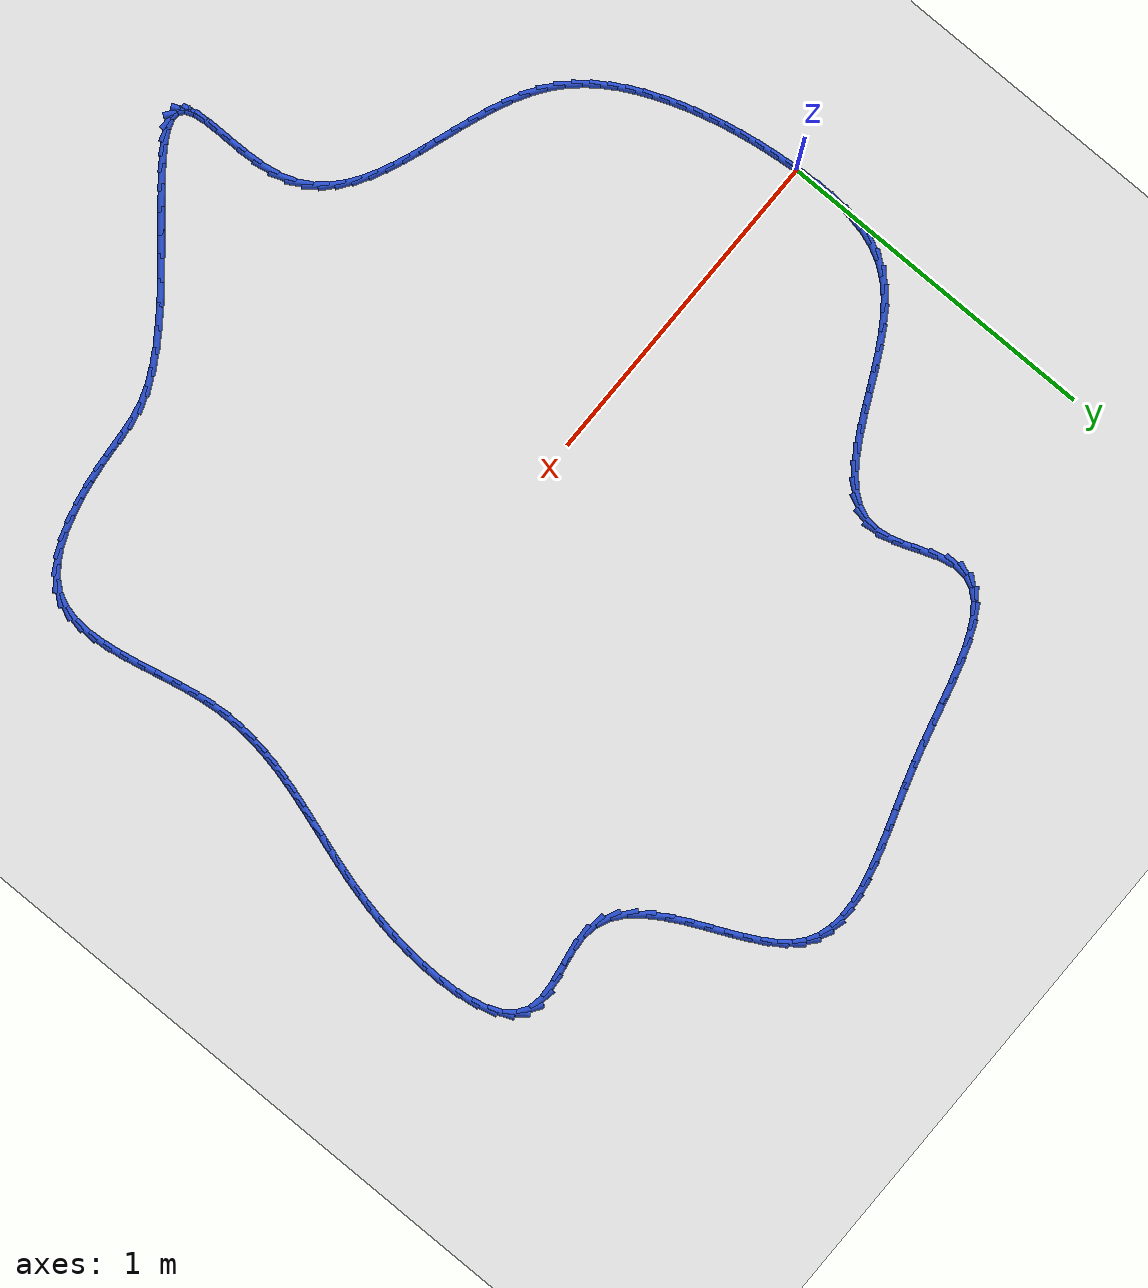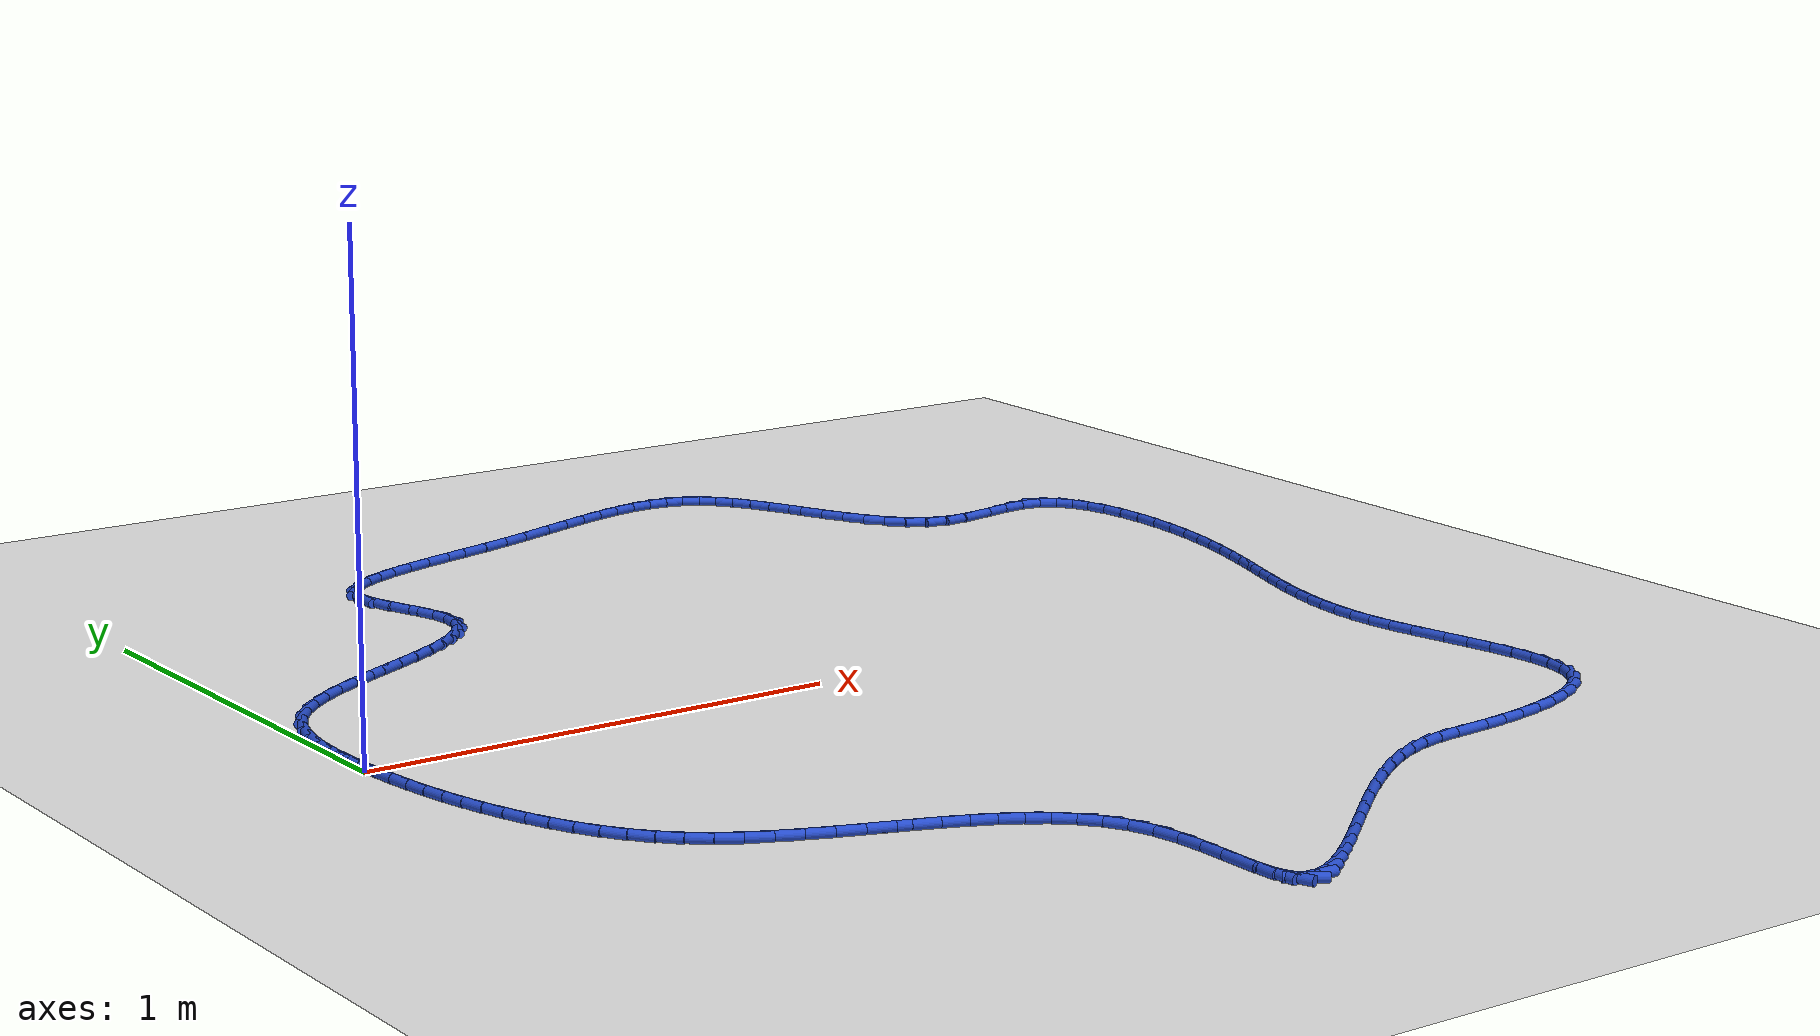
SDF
<sdf version="1.6">
 <world name="default">
  <light name="sun" type="directional">
   <pose>0 0 10 0 -0 0</pose>
   <diffuse>0.8 0.8 0.8 1</diffuse>
   <specular>0.2 0.2 0.2 1</specular>
   <attenuation>
    <range>1000</range>
    <constant>0.9</constant>
    <linear>0.01</linear>
    <quadratic>0.001</quadratic>
   </attenuation>
   <direction>-0.5 0.1 -0.9</direction>
  </light>
  <model name="ground_plane">
   <static>1</static>
   <link name="link">
    <collision name="collision">
     <geometry><plane><normal>0 0 1</normal><size>100 100</size></plane></geometry>
     <surface><friction><ode><mu>100</mu><mu2>50</mu2></ode></friction></surface>
    </collision>
    <visual name="visual">
     <cast_shadows>0</cast_shadows>
     <geometry><plane><normal>0 0 1</normal><size>100 100</size></plane></geometry>
     <material>
      <script><uri>file://media/materials/scripts/gazebo.material</uri><name>Gazebo/WhiteGlow</name></script>
     </material>
    </visual>
   </link>
  </model>
  <gravity>0 0 -9.8</gravity>
  <magnetic_field>6e-06 2.3e-05 -4.2e-05</magnetic_field>
  <atmosphere type="adiabatic"/>
  <physics name="default_physics" default="0" type="ode">
   <max_step_size>0.001</max_step_size>
   <real_time_factor>1</real_time_factor>
   <real_time_update_rate>1000</real_time_update_rate>
  </physics>
  <scene><ambient>0.4 0.4 0.4 1</ambient><background>0.7 0.7 0.7 1</background><shadows>1</shadows></scene>
  <spherical_coordinates>
   <surface_model>EARTH_WGS84</surface_model>
   <latitude_deg>0</latitude_deg>
   <longitude_deg>0</longitude_deg>
   <elevation>0</elevation>
   <heading_deg>0</heading_deg>
  </spherical_coordinates>
  <model name="line">
   <link name="link_0">
    <pose>1.6263032587282567e-17 1.3877787807814457e-17 0.01 0 1.57 -1.513585574308806</pose>
    <collision name="collision">
     <geometry><cylinder><radius>0.01</radius><length>0.08</length></cylinder></geometry>
    </collision>
    <visual name="visual">
     <material>
      <script><name>Gazebo/Blue</name><uri>file://media/materials/scripts/gazebo.material</uri></script>
     </material>
     <geometry><cylinder><radius>0.01</radius><length>0.08</length></cylinder></geometry>
    </visual>
   </link>
   <link name="link_1">
    <pose>-0.002925904967437072 0.051086761017259785 0.01 0 1.57 -1.5534604865196697</pose>
    <collision name="collision">
     <geometry><cylinder><radius>0.01</radius><length>0.08</length></cylinder></geometry>
    </collision>
    <visual name="visual">
     <material>
      <script><name>Gazebo/Blue</name><uri>file://media/materials/scripts/gazebo.material</uri></script>
     </material>
     <geometry><cylinder><radius>0.01</radius><length>0.08</length></cylinder></geometry>
    </visual>
   </link>
   <link name="link_2">
    <pose>-0.003817468521577585 0.1025105295758779 0.01 0 1.57 1.5309589534957653</pose>
    <collision name="collision">
     <geometry><cylinder><radius>0.01</radius><length>0.08</length></cylinder></geometry>
    </collision>
    <visual name="visual">
     <material>
      <script><name>Gazebo/Blue</name><uri>file://media/materials/scripts/gazebo.material</uri></script>
     </material>
     <geometry><cylinder><radius>0.01</radius><length>0.08</length></cylinder></geometry>
    </visual>
   </link>
   <link name="link_3">
    <pose>-0.0017811809256003527 0.15359849311952 0.01 0 1.57 1.4543580626659827</pose>
    <collision name="collision">
     <geometry><cylinder><radius>0.01</radius><length>0.08</length></cylinder></geometry>
    </collision>
    <visual name="visual">
     <material>
      <script><name>Gazebo/Blue</name><uri>file://media/materials/scripts/gazebo.material</uri></script>
     </material>
     <geometry><cylinder><radius>0.01</radius><length>0.08</length></cylinder></geometry>
    </visual>
   </link>
   <link name="link_4">
    <pose>0.004076467557315798 0.20367783909185186 0.01 0 1.57 1.3557250557406852</pose>
    <collision name="collision">
     <geometry><cylinder><radius>0.01</radius><length>0.08</length></cylinder></geometry>
    </collision>
    <visual name="visual">
     <material>
      <script><name>Gazebo/Blue</name><uri>file://media/materials/scripts/gazebo.material</uri></script>
     </material>
     <geometry><cylinder><radius>0.01</radius><length>0.08</length></cylinder></geometry>
    </visual>
   </link>
   <link name="link_5">
    <pose>0.014648986663992034 0.25207575493653933 0.01 0 1.57 1.2328525527008483</pose>
    <collision name="collision">
     <geometry><cylinder><radius>0.01</radius><length>0.08</length></cylinder></geometry>
    </collision>
    <visual name="visual">
     <material>
      <script><name>Gazebo/Blue</name><uri>file://media/materials/scripts/gazebo.material</uri></script>
     </material>
     <geometry><cylinder><radius>0.01</radius><length>0.08</length></cylinder></geometry>
    </visual>
   </link>
   <link name="link_6">
    <pose>0.03082988613124953 0.29811942809724795 0.01 0 1.57 1.0855456857132073</pose>
    <collision name="collision">
     <geometry><cylinder><radius>0.01</radius><length>0.08</length></cylinder></geometry>
    </collision>
    <visual name="visual">
     <material>
      <script><name>Gazebo/Blue</name><uri>file://media/materials/scripts/gazebo.material</uri></script>
     </material>
     <geometry><cylinder><radius>0.01</radius><length>0.08</length></cylinder></geometry>
    </visual>
   </link>
   <link name="link_7">
    <pose>0.053512675695909465 0.3411360460176436 0.01 0 1.57 0.918838790433517</pose>
    <collision name="collision">
     <geometry><cylinder><radius>0.01</radius><length>0.08</length></cylinder></geometry>
    </collision>
    <visual name="visual">
     <material>
      <script><name>Gazebo/Blue</name><uri>file://media/materials/scripts/gazebo.material</uri></script>
     </material>
     <geometry><cylinder><radius>0.01</radius><length>0.08</length></cylinder></geometry>
    </visual>
   </link>
   <link name="link_8">
    <pose>0.08354329892548039 0.38047930402325114 0.01 0 1.57 0.764667883301005</pose>
    <collision name="collision">
     <geometry><cylinder><radius>0.01</radius><length>0.08</length></cylinder></geometry>
    </collision>
    <visual name="visual">
     <material>
      <script><name>Gazebo/Blue</name><uri>file://media/materials/scripts/gazebo.material</uri></script>
     </material>
     <geometry><cylinder><radius>0.01</radius><length>0.08</length></cylinder></geometry>
    </visual>
   </link>
   <link name="link_9">
    <pose>0.12068112088730405 0.4161084306353329 0.01 0 1.57 0.6477522191212495</pose>
    <collision name="collision">
     <geometry><cylinder><radius>0.01</radius><length>0.08</length></cylinder></geometry>
    </collision>
    <visual name="visual">
     <material>
      <script><name>Gazebo/Blue</name><uri>file://media/materials/scripts/gazebo.material</uri></script>
     </material>
     <geometry><cylinder><radius>0.01</radius><length>0.08</length></cylinder></geometry>
    </visual>
   </link>
   <link name="link_10">
    <pose>0.16360304735045483 0.4485858920041277 0.01 0 1.57 0.5635845289567744</pose>
    <collision name="collision">
     <geometry><cylinder><radius>0.01</radius><length>0.08</length></cylinder></geometry>
    </collision>
    <visual name="visual">
     <material>
      <script><name>Gazebo/Blue</name><uri>file://media/materials/scripts/gazebo.material</uri></script>
     </material>
     <geometry><cylinder><radius>0.01</radius><length>0.08</length></cylinder></geometry>
    </visual>
   </link>
   <link name="link_11">
    <pose>0.21093924175880024 0.4785002030463036 0.01 0 1.57 0.5063464724308085</pose>
    <collision name="collision">
     <geometry><cylinder><radius>0.01</radius><length>0.08</length></cylinder></geometry>
    </collision>
    <visual name="visual">
     <material>
      <script><name>Gazebo/Blue</name><uri>file://media/materials/scripts/gazebo.material</uri></script>
     </material>
     <geometry><cylinder><radius>0.01</radius><length>0.08</length></cylinder></geometry>
    </visual>
   </link>
   <link name="link_12">
    <pose>0.2613198675562078 0.5064398786785287 0.01 0 1.57 0.4716977754873825</pose>
    <collision name="collision">
     <geometry><cylinder><radius>0.01</radius><length>0.08</length></cylinder></geometry>
    </collision>
    <visual name="visual">
     <material>
      <script><name>Gazebo/Blue</name><uri>file://media/materials/scripts/gazebo.material</uri></script>
     </material>
     <geometry><cylinder><radius>0.01</radius><length>0.08</length></cylinder></geometry>
    </visual>
   </link>
   <link name="link_13">
    <pose>0.31337508818654486 0.5329934338174719 0.01 0 1.57 0.45714780488812573</pose>
    <collision name="collision">
     <geometry><cylinder><radius>0.01</radius><length>0.08</length></cylinder></geometry>
    </collision>
    <visual name="visual">
     <material>
      <script><name>Gazebo/Blue</name><uri>file://media/materials/scripts/gazebo.material</uri></script>
     </material>
     <geometry><cylinder><radius>0.01</radius><length>0.08</length></cylinder></geometry>
    </visual>
   </link>
   <link name="link_14">
    <pose>0.3657350670936789 0.5587493833798008 0.01 0 1.57 0.4620775457771259</pose>
    <collision name="collision">
     <geometry><cylinder><radius>0.01</radius><length>0.08</length></cylinder></geometry>
    </collision>
    <visual name="visual">
     <material>
      <script><name>Gazebo/Blue</name><uri>file://media/materials/scripts/gazebo.material</uri></script>
     </material>
     <geometry><cylinder><radius>0.01</radius><length>0.08</length></cylinder></geometry>
    </visual>
   </link>
   <link name="link_15">
    <pose>0.41702996772147727 0.5842962422821845 0.01 0 1.57 0.48784564405269903</pose>
    <collision name="collision">
     <geometry><cylinder><radius>0.01</radius><length>0.08</length></cylinder></geometry>
    </collision>
    <visual name="visual">
     <material>
      <script><name>Gazebo/Blue</name><uri>file://media/materials/scripts/gazebo.material</uri></script>
     </material>
     <geometry><cylinder><radius>0.01</radius><length>0.08</length></cylinder></geometry>
    </visual>
   </link>
   <link name="link_16">
    <pose>0.46588995351380774 0.610222525441291 0.01 0 1.57 0.5381492918049732</pose>
    <collision name="collision">
     <geometry><cylinder><radius>0.01</radius><length>0.08</length></cylinder></geometry>
    </collision>
    <visual name="visual">
     <material>
      <script><name>Gazebo/Blue</name><uri>file://media/materials/scripts/gazebo.material</uri></script>
     </material>
     <geometry><cylinder><radius>0.01</radius><length>0.08</length></cylinder></geometry>
    </visual>
   </link>
   <link name="link_17">
    <pose>0.5109451879145376 0.6371167477737885 0.01 0 1.57 0.6196598165027448</pose>
    <collision name="collision">
     <geometry><cylinder><radius>0.01</radius><length>0.08</length></cylinder></geometry>
    </collision>
    <visual name="visual">
     <material>
      <script><name>Gazebo/Blue</name><uri>file://media/materials/scripts/gazebo.material</uri></script>
     </material>
     <geometry><cylinder><radius>0.01</radius><length>0.08</length></cylinder></geometry>
    </visual>
   </link>
   <link name="link_18">
    <pose>0.5508258343675341 0.6655674241963453 0.01 0 1.57 0.7425572486324425</pose>
    <collision name="collision">
     <geometry><cylinder><radius>0.01</radius><length>0.08</length></cylinder></geometry>
    </collision>
    <visual name="visual">
     <material>
      <script><name>Gazebo/Blue</name><uri>file://media/materials/scripts/gazebo.material</uri></script>
     </material>
     <geometry><cylinder><radius>0.01</radius><length>0.08</length></cylinder></geometry>
    </visual>
   </link>
   <link name="link_19">
    <pose>0.5841620563166647 0.6961630696256299 0.01 0 1.57 0.9191818545421</pose>
    <collision name="collision">
     <geometry><cylinder><radius>0.01</radius><length>0.08</length></cylinder></geometry>
    </collision>
    <visual name="visual">
     <material>
      <script><name>Gazebo/Blue</name><uri>file://media/materials/scripts/gazebo.material</uri></script>
     </material>
     <geometry><cylinder><radius>0.01</radius><length>0.08</length></cylinder></geometry>
    </visual>
   </link>
   <link name="link_20">
    <pose>0.6095840172057972 0.729492198978311 0.01 0 1.57 1.1560296487038075</pose>
    <collision name="collision">
     <geometry><cylinder><radius>0.01</radius><length>0.08</length></cylinder></geometry>
    </collision>
    <visual name="visual">
     <material>
      <script><name>Gazebo/Blue</name><uri>file://media/materials/scripts/gazebo.material</uri></script>
     </material>
     <geometry><cylinder><radius>0.01</radius><length>0.08</length></cylinder></geometry>
    </visual>
   </link>
   <link name="link_21">
    <pose>0.6257218804787988 0.7661433271710562 0.01 0 1.57 1.4364113022254412</pose>
    <collision name="collision">
     <geometry><cylinder><radius>0.01</radius><length>0.08</length></cylinder></geometry>
    </collision>
    <visual name="visual">
     <material>
      <script><name>Gazebo/Blue</name><uri>file://media/materials/scripts/gazebo.material</uri></script>
     </material>
     <geometry><cylinder><radius>0.01</radius><length>0.08</length></cylinder></geometry>
    </visual>
   </link>
   <link name="link_22">
    <pose>0.6312058095795372 0.8067049691205342 0.01 0 1.57 -1.433663674513513</pose>
    <collision name="collision">
     <geometry><cylinder><radius>0.01</radius><length>0.08</length></cylinder></geometry>
    </collision>
    <visual name="visual">
     <material>
      <script><name>Gazebo/Blue</name><uri>file://media/materials/scripts/gazebo.material</uri></script>
     </material>
     <geometry><cylinder><radius>0.01</radius><length>0.08</length></cylinder></geometry>
    </visual>
   </link>
   <link name="link_23">
    <pose>0.6250069916845122 0.8516243371982805 0.01 0 1.57 -1.268252917757996</pose>
    <collision name="collision">
     <geometry><cylinder><radius>0.01</radius><length>0.08</length></cylinder></geometry>
    </collision>
    <visual name="visual">
     <material>
      <script><name>Gazebo/Blue</name><uri>file://media/materials/scripts/gazebo.material</uri></script>
     </material>
     <geometry><cylinder><radius>0.01</radius><length>0.08</length></cylinder></geometry>
    </visual>
   </link>
   <link name="link_24">
    <pose>0.6099903521537846 0.8997352806495409 0.01 0 1.57 -1.210693850976044</pose>
    <collision name="collision">
     <geometry><cylinder><radius>0.01</radius><length>0.08</length></cylinder></geometry>
    </collision>
    <visual name="visual">
     <material>
      <script><name>Gazebo/Blue</name><uri>file://media/materials/scripts/gazebo.material</uri></script>
     </material>
     <geometry><cylinder><radius>0.01</radius><length>0.08</length></cylinder></geometry>
    </visual>
   </link>
   <link name="link_25">
    <pose>0.5914997541546244 0.9488445054803473 0.01 0 1.57 -1.237535827203266</pose>
    <collision name="collision">
     <geometry><cylinder><radius>0.01</radius><length>0.08</length></cylinder></geometry>
    </collision>
    <visual name="visual">
     <material>
      <script><name>Gazebo/Blue</name><uri>file://media/materials/scripts/gazebo.material</uri></script>
     </material>
     <geometry><cylinder><radius>0.01</radius><length>0.08</length></cylinder></geometry>
    </visual>
   </link>
   <link name="link_26">
    <pose>0.5749189122884097 0.9967422053296207 0.01 0 1.57 -1.3649385275086428</pose>
    <collision name="collision">
     <geometry><cylinder><radius>0.01</radius><length>0.08</length></cylinder></geometry>
    </collision>
    <visual name="visual">
     <material>
      <script><name>Gazebo/Blue</name><uri>file://media/materials/scripts/gazebo.material</uri></script>
     </material>
     <geometry><cylinder><radius>0.01</radius><length>0.08</length></cylinder></geometry>
    </visual>
   </link>
   <link name="link_27">
    <pose>0.5656315411565188 1.0412185738362816 0.01 0 1.57 1.5066469889825602</pose>
    <collision name="collision">
     <geometry><cylinder><radius>0.01</radius><length>0.08</length></cylinder></geometry>
    </collision>
    <visual name="visual">
     <material>
      <script><name>Gazebo/Blue</name><uri>file://media/materials/scripts/gazebo.material</uri></script>
     </material>
     <geometry><cylinder><radius>0.01</radius><length>0.08</length></cylinder></geometry>
    </visual>
   </link>
   <link name="link_28">
    <pose>0.5681508647052947 1.0804374792606255 0.01 0 1.57 1.1698672302090587</pose>
    <collision name="collision">
     <geometry><cylinder><radius>0.01</radius><length>0.08</length></cylinder></geometry>
    </collision>
    <visual name="visual">
     <material>
      <script><name>Gazebo/Blue</name><uri>file://media/materials/scripts/gazebo.material</uri></script>
     </material>
     <geometry><cylinder><radius>0.01</radius><length>0.08</length></cylinder></geometry>
    </visual>
   </link>
   <link name="link_29">
    <pose>0.5825722993843526 1.114459217508778 0.01 0 1.57 0.8671177979331303</pose>
    <collision name="collision">
     <geometry><cylinder><radius>0.01</radius><length>0.08</length></cylinder></geometry>
    </collision>
    <visual name="visual">
     <material>
      <script><name>Gazebo/Blue</name><uri>file://media/materials/scripts/gazebo.material</uri></script>
     </material>
     <geometry><cylinder><radius>0.01</radius><length>0.08</length></cylinder></geometry>
    </visual>
   </link>
   <link name="link_30">
    <pose>0.6075931768705176 1.1439442388884058 0.01 0 1.57 0.641094063068548</pose>
    <collision name="collision">
     <geometry><cylinder><radius>0.01</radius><length>0.08</length></cylinder></geometry>
    </collision>
    <visual name="visual">
     <material>
      <script><name>Gazebo/Blue</name><uri>file://media/materials/scripts/gazebo.material</uri></script>
     </material>
     <geometry><cylinder><radius>0.01</radius><length>0.08</length></cylinder></geometry>
    </visual>
   </link>
   <link name="link_31">
    <pose>0.6419102780174444 1.1695532301584692 0.01 0 1.57 0.4867917874702019</pose>
    <collision name="collision">
     <geometry><cylinder><radius>0.01</radius><length>0.08</length></cylinder></geometry>
    </collision>
    <visual name="visual">
     <material>
      <script><name>Gazebo/Blue</name><uri>file://media/materials/scripts/gazebo.material</uri></script>
     </material>
     <geometry><cylinder><radius>0.01</radius><length>0.08</length></cylinder></geometry>
    </visual>
   </link>
   <link name="link_32">
    <pose>0.684220383678787 1.1919468780779283 0.01 0 1.57 0.38470469914114663</pose>
    <collision name="collision">
     <geometry><cylinder><radius>0.01</radius><length>0.08</length></cylinder></geometry>
    </collision>
    <visual name="visual">
     <material>
      <script><name>Gazebo/Blue</name><uri>file://media/materials/scripts/gazebo.material</uri></script>
     </material>
     <geometry><cylinder><radius>0.01</radius><length>0.08</length></cylinder></geometry>
    </visual>
   </link>
   <link name="link_33">
    <pose>0.7332202747081993 1.2117858694057422 0.01 0 1.57 0.3187059509382366</pose>
    <collision name="collision">
     <geometry><cylinder><radius>0.01</radius><length>0.08</length></cylinder></geometry>
    </collision>
    <visual name="visual">
     <material>
      <script><name>Gazebo/Blue</name><uri>file://media/materials/scripts/gazebo.material</uri></script>
     </material>
     <geometry><cylinder><radius>0.01</radius><length>0.08</length></cylinder></geometry>
    </visual>
   </link>
   <link name="link_34">
    <pose>0.787606731959336 1.229730890900871 0.01 0 1.57 0.27839579438513723</pose>
    <collision name="collision">
     <geometry><cylinder><radius>0.01</radius><length>0.08</length></cylinder></geometry>
    </collision>
    <visual name="visual">
     <material>
      <script><name>Gazebo/Blue</name><uri>file://media/materials/scripts/gazebo.material</uri></script>
     </material>
     <geometry><cylinder><radius>0.01</radius><length>0.08</length></cylinder></geometry>
    </visual>
   </link>
   <link name="link_35">
    <pose>0.8460765362858507 1.2464426293222741 0.01 0 1.57 0.2576403532458048</pose>
    <collision name="collision">
     <geometry><cylinder><radius>0.01</radius><length>0.08</length></cylinder></geometry>
    </collision>
    <visual name="visual">
     <material>
      <script><name>Gazebo/Blue</name><uri>file://media/materials/scripts/gazebo.material</uri></script>
     </material>
     <geometry><cylinder><radius>0.01</radius><length>0.08</length></cylinder></geometry>
    </visual>
   </link>
   <link name="link_36">
    <pose>0.9073264685413981 1.2625817714289114 0.01 0 1.57 0.25314698224797855</pose>
    <collision name="collision">
     <geometry><cylinder><radius>0.01</radius><length>0.08</length></cylinder></geometry>
    </collision>
    <visual name="visual">
     <material>
      <script><name>Gazebo/Blue</name><uri>file://media/materials/scripts/gazebo.material</uri></script>
     </material>
     <geometry><cylinder><radius>0.01</radius><length>0.08</length></cylinder></geometry>
    </visual>
   </link>
   <link name="link_37">
    <pose>0.9700533095796322 1.2788090039797426 0.01 0 1.57 0.26360612759117724</pose>
    <collision name="collision">
     <geometry><cylinder><radius>0.01</radius><length>0.08</length></cylinder></geometry>
    </collision>
    <visual name="visual">
     <material>
      <script><name>Gazebo/Blue</name><uri>file://media/materials/scripts/gazebo.material</uri></script>
     </material>
     <geometry><cylinder><radius>0.01</radius><length>0.08</length></cylinder></geometry>
    </visual>
   </link>
   <link name="link_38">
    <pose>1.0329538402542071 1.2957850137337277 0.01 0 1.57 0.28773147898943485</pose>
    <collision name="collision">
     <geometry><cylinder><radius>0.01</radius><length>0.08</length></cylinder></geometry>
    </collision>
    <visual name="visual">
     <material>
      <script><name>Gazebo/Blue</name><uri>file://media/materials/scripts/gazebo.material</uri></script>
     </material>
     <geometry><cylinder><radius>0.01</radius><length>0.08</length></cylinder></geometry>
    </visual>
   </link>
   <link name="link_39">
    <pose>1.0947882218757106 1.3140845230467404 0.01 0 1.57 0.3101198656704801</pose>
    <collision name="collision">
     <geometry><cylinder><radius>0.01</radius><length>0.08</length></cylinder></geometry>
    </collision>
    <visual name="visual">
     <material>
      <script><name>Gazebo/Blue</name><uri>file://media/materials/scripts/gazebo.material</uri></script>
     </material>
     <geometry><cylinder><radius>0.01</radius><length>0.08</length></cylinder></geometry>
    </visual>
   </link>
   <link name="link_40">
    <pose>1.1549853256258091 1.3333752673628163 0.01 0 1.57 0.32086154427678587</pose>
    <collision name="collision">
     <geometry><cylinder><radius>0.01</radius><length>0.08</length></cylinder></geometry>
    </collision>
    <visual name="visual">
     <material>
      <script><name>Gazebo/Blue</name><uri>file://media/materials/scripts/gazebo.material</uri></script>
     </material>
     <geometry><cylinder><radius>0.01</radius><length>0.08</length></cylinder></geometry>
    </visual>
   </link>
   <link name="link_41">
    <pose>1.2133751744726042 1.3527808905315764 0.01 0 1.57 0.31904794317265384</pose>
    <collision name="collision">
     <geometry><cylinder><radius>0.01</radius><length>0.08</length></cylinder></geometry>
    </collision>
    <visual name="visual">
     <material>
      <script><name>Gazebo/Blue</name><uri>file://media/materials/scripts/gazebo.material</uri></script>
     </material>
     <geometry><cylinder><radius>0.01</radius><length>0.08</length></cylinder></geometry>
    </visual>
   </link>
   <link name="link_42">
    <pose>1.2697932398542697 1.3714176465146504 0.01 0 1.57 0.3032388721224452</pose>
    <collision name="collision">
     <geometry><cylinder><radius>0.01</radius><length>0.08</length></cylinder></geometry>
    </collision>
    <visual name="visual">
     <material>
      <script><name>Gazebo/Blue</name><uri>file://media/materials/scripts/gazebo.material</uri></script>
     </material>
     <geometry><cylinder><radius>0.01</radius><length>0.08</length></cylinder></geometry>
    </visual>
   </link>
   <link name="link_43">
    <pose>1.3240749932089795 1.388401789273668 0.01 0 1.57 0.27110117103073994</pose>
    <collision name="collision">
     <geometry><cylinder><radius>0.01</radius><length>0.08</length></cylinder></geometry>
    </collision>
    <visual name="visual">
     <material>
      <script><name>Gazebo/Blue</name><uri>file://media/materials/scripts/gazebo.material</uri></script>
     </material>
     <geometry><cylinder><radius>0.01</radius><length>0.08</length></cylinder></geometry>
    </visual>
   </link>
   <link name="link_44">
    <pose>1.3760559059749082 1.40284957277026 0.01 0 1.57 0.2191350966766762</pose>
    <collision name="collision">
     <geometry><cylinder><radius>0.01</radius><length>0.08</length></cylinder></geometry>
    </collision>
    <visual name="visual">
     <material>
      <script><name>Gazebo/Blue</name><uri>file://media/materials/scripts/gazebo.material</uri></script>
     </material>
     <geometry><cylinder><radius>0.01</radius><length>0.08</length></cylinder></geometry>
    </visual>
   </link>
   <link name="link_45">
    <pose>1.4255714495902292 1.413877250966055 0.01 0 1.57 0.14243790097048115</pose>
    <collision name="collision">
     <geometry><cylinder><radius>0.01</radius><length>0.08</length></cylinder></geometry>
    </collision>
    <visual name="visual">
     <material>
      <script><name>Gazebo/Blue</name><uri>file://media/materials/scripts/gazebo.material</uri></script>
     </material>
     <geometry><cylinder><radius>0.01</radius><length>0.08</length></cylinder></geometry>
    </visual>
   </link>
   <link name="link_46">
    <pose>1.4724570954931167 1.4206010778226845 0.01 0 1.57 0.03482798386878905</pose>
    <collision name="collision">
     <geometry><cylinder><radius>0.01</radius><length>0.08</length></cylinder></geometry>
    </collision>
    <visual name="visual">
     <material>
      <script><name>Gazebo/Blue</name><uri>file://media/materials/scripts/gazebo.material</uri></script>
     </material>
     <geometry><cylinder><radius>0.01</radius><length>0.08</length></cylinder></geometry>
    </visual>
   </link>
   <link name="link_47">
    <pose>1.5165483151217447 1.4221373073017776 0.01 0 1.57 -0.1098132986529564</pose>
    <collision name="collision">
     <geometry><cylinder><radius>0.01</radius><length>0.08</length></cylinder></geometry>
    </collision>
    <visual name="visual">
     <material>
      <script><name>Gazebo/Blue</name><uri>file://media/materials/scripts/gazebo.material</uri></script>
     </material>
     <geometry><cylinder><radius>0.01</radius><length>0.08</length></cylinder></geometry>
    </visual>
   </link>
   <link name="link_48">
    <pose>1.5576805799142872 1.4176021933649643 0.01 0 1.57 -0.2935691346779938</pose>
    <collision name="collision">
     <geometry><cylinder><radius>0.01</radius><length>0.08</length></cylinder></geometry>
    </collision>
    <visual name="visual">
     <material>
      <script><name>Gazebo/Blue</name><uri>file://media/materials/scripts/gazebo.material</uri></script>
     </material>
     <geometry><cylinder><radius>0.01</radius><length>0.08</length></cylinder></geometry>
    </visual>
   </link>
   <link name="link_49">
    <pose>1.5956893613089176 1.4061119899738745 0.01 0 1.57 -0.5079723118283043</pose>
    <collision name="collision">
     <geometry><cylinder><radius>0.01</radius><length>0.08</length></cylinder></geometry>
    </collision>
    <visual name="visual">
     <material>
      <script><name>Gazebo/Blue</name><uri>file://media/materials/scripts/gazebo.material</uri></script>
     </material>
     <geometry><cylinder><radius>0.01</radius><length>0.08</length></cylinder></geometry>
    </visual>
   </link>
   <link name="link_50">
    <pose>1.6304101307438112 1.3867829510901386 0.01 0 1.57 -0.7303041335675124</pose>
    <collision name="collision">
     <geometry><cylinder><radius>0.01</radius><length>0.08</length></cylinder></geometry>
    </collision>
    <visual name="visual">
     <material>
      <script><name>Gazebo/Blue</name><uri>file://media/materials/scripts/gazebo.material</uri></script>
     </material>
     <geometry><cylinder><radius>0.01</radius><length>0.08</length></cylinder></geometry>
    </visual>
   </link>
   <link name="link_51">
    <pose>1.6616923494191098 1.3587708070804276 0.01 0 1.57 -0.9119578785659509</pose>
    <collision name="collision">
     <geometry><cylinder><radius>0.01</radius><length>0.08</length></cylinder></geometry>
    </collision>
    <visual name="visual">
     <material>
      <script><name>Gazebo/Blue</name><uri>file://media/materials/scripts/gazebo.material</uri></script>
     </material>
     <geometry><cylinder><radius>0.01</radius><length>0.08</length></cylinder></geometry>
    </visual>
   </link>
   <link name="link_52">
    <pose>1.6898161751977725 1.322446631070586 0.01 0 1.57 -1.0297347315521022</pose>
    <collision name="collision">
     <geometry><cylinder><radius>0.01</radius><length>0.08</length></cylinder></geometry>
    </collision>
    <visual name="visual">
     <material>
      <script><name>Gazebo/Blue</name><uri>file://media/materials/scripts/gazebo.material</uri></script>
     </material>
     <geometry><cylinder><radius>0.01</radius><length>0.08</length></cylinder></geometry>
    </visual>
   </link>
   <link name="link_53">
    <pose>1.7155633926999772 1.279596989966249 0.01 0 1.57 -1.0999959998668456</pose>
    <collision name="collision">
     <geometry><cylinder><radius>0.01</radius><length>0.08</length></cylinder></geometry>
    </collision>
    <visual name="visual">
     <material>
      <script><name>Gazebo/Blue</name><uri>file://media/materials/scripts/gazebo.material</uri></script>
     </material>
     <geometry><cylinder><radius>0.01</radius><length>0.08</length></cylinder></geometry>
    </visual>
   </link>
   <link name="link_54">
    <pose>1.7397440657627796 1.2320882491587057 0.01 0 1.57 -1.1349829347576557</pose>
    <collision name="collision">
     <geometry><cylinder><radius>0.01</radius><length>0.08</length></cylinder></geometry>
    </collision>
    <visual name="visual">
     <material>
      <script><name>Gazebo/Blue</name><uri>file://media/materials/scripts/gazebo.material</uri></script>
     </material>
     <geometry><cylinder><radius>0.01</radius><length>0.08</length></cylinder></geometry>
    </visual>
   </link>
   <link name="link_55">
    <pose>1.7631682582232375 1.181786774039246 0.01 0 1.57 -1.1410607110863586</pose>
    <collision name="collision">
     <geometry><cylinder><radius>0.01</radius><length>0.08</length></cylinder></geometry>
    </collision>
    <visual name="visual">
     <material>
      <script><name>Gazebo/Blue</name><uri>file://media/materials/scripts/gazebo.material</uri></script>
     </material>
     <geometry><cylinder><radius>0.01</radius><length>0.08</length></cylinder></geometry>
    </visual>
   </link>
   <link name="link_56">
    <pose>1.786646033918407 1.1305589299991607 0.01 0 1.57 -1.1199965464238453</pose>
    <collision name="collision">
     <geometry><cylinder><radius>0.01</radius><length>0.08</length></cylinder></geometry>
    </collision>
    <visual name="visual">
     <material>
      <script><name>Gazebo/Blue</name><uri>file://media/materials/scripts/gazebo.material</uri></script>
     </material>
     <geometry><cylinder><radius>0.01</radius><length>0.08</length></cylinder></geometry>
    </visual>
   </link>
   <link name="link_57">
    <pose>1.810987456685345 1.0802710824297397 0.01 0 1.57 -1.0695663815188812</pose>
    <collision name="collision">
     <geometry><cylinder><radius>0.01</radius><length>0.08</length></cylinder></geometry>
    </collision>
    <visual name="visual">
     <material>
      <script><name>Gazebo/Blue</name><uri>file://media/materials/scripts/gazebo.material</uri></script>
     </material>
     <geometry><cylinder><radius>0.01</radius><length>0.08</length></cylinder></geometry>
    </visual>
   </link>
   <link name="link_58">
    <pose>1.8370025903611087 1.0327895967222729 0.01 0 1.57 -0.983445157615883</pose>
    <collision name="collision">
     <geometry><cylinder><radius>0.01</radius><length>0.08</length></cylinder></geometry>
    </collision>
    <visual name="visual">
     <material>
      <script><name>Gazebo/Blue</name><uri>file://media/materials/scripts/gazebo.material</uri></script>
     </material>
     <geometry><cylinder><radius>0.01</radius><length>0.08</length></cylinder></geometry>
    </visual>
   </link>
   <link name="link_59">
    <pose>1.8655014987827543 0.9899808382680507 0.01 0 1.57 -0.8510802155269899</pose>
    <collision name="collision">
     <geometry><cylinder><radius>0.01</radius><length>0.08</length></cylinder></geometry>
    </collision>
    <visual name="visual">
     <material>
      <script><name>Gazebo/Blue</name><uri>file://media/materials/scripts/gazebo.material</uri></script>
     </material>
     <geometry><cylinder><radius>0.01</radius><length>0.08</length></cylinder></geometry>
    </visual>
   </link>
   <link name="link_60">
    <pose>1.8972942457873394 0.9537111724583636 0.01 0 1.57 -0.660080695817832</pose>
    <collision name="collision">
     <geometry><cylinder><radius>0.01</radius><length>0.08</length></cylinder></geometry>
    </collision>
    <visual name="visual">
     <material>
      <script><name>Gazebo/Blue</name><uri>file://media/materials/scripts/gazebo.material</uri></script>
     </material>
     <geometry><cylinder><radius>0.01</radius><length>0.08</length></cylinder></geometry>
    </visual>
   </link>
   <link name="link_61">
    <pose>1.9331908952119206 0.9258469646845007 0.01 0 1.57 -0.407003883285448</pose>
    <collision name="collision">
     <geometry><cylinder><radius>0.01</radius><length>0.08</length></cylinder></geometry>
    </collision>
    <visual name="visual">
     <material>
      <script><name>Gazebo/Blue</name><uri>file://media/materials/scripts/gazebo.material</uri></script>
     </material>
     <geometry><cylinder><radius>0.01</radius><length>0.08</length></cylinder></geometry>
    </visual>
   </link>
   <link name="link_62">
    <pose>1.9740015108935538 0.9082545803377529 0.01 0 1.57 -0.12229285884908145</pose>
    <collision name="collision">
     <geometry><cylinder><radius>0.01</radius><length>0.08</length></cylinder></geometry>
    </collision>
    <visual name="visual">
     <material>
      <script><name>Gazebo/Blue</name><uri>file://media/materials/scripts/gazebo.material</uri></script>
     </material>
     <geometry><cylinder><radius>0.01</radius><length>0.08</length></cylinder></geometry>
    </visual>
   </link>
   <link name="link_63">
    <pose>2.0204100396931026 0.9025506853351482 0.01 0 1.57 0.07956466956215329</pose>
    <collision name="collision">
     <geometry><cylinder><radius>0.01</radius><length>0.08</length></cylinder></geometry>
    </collision>
    <visual name="visual">
     <material>
      <script><name>Gazebo/Blue</name><uri>file://media/materials/scripts/gazebo.material</uri></script>
     </material>
     <geometry><cylinder><radius>0.01</radius><length>0.08</length></cylinder></geometry>
    </visual>
   </link>
   <link name="link_64">
    <pose>2.0712058103587356 0.9066007840852384 0.01 0 1.57 0.16556797552031732</pose>
    <collision name="collision">
     <geometry><cylinder><radius>0.01</radius><length>0.08</length></cylinder></geometry>
    </collision>
    <visual name="visual">
     <material>
      <script><name>Gazebo/Blue</name><uri>file://media/materials/scripts/gazebo.material</uri></script>
     </material>
     <geometry><cylinder><radius>0.01</radius><length>0.08</length></cylinder></geometry>
    </visual>
   </link>
   <link name="link_65">
    <pose>2.123715807744107 0.9153750808342276 0.01 0 1.57 0.1615241554821695</pose>
    <collision name="collision">
     <geometry><cylinder><radius>0.01</radius><length>0.08</length></cylinder></geometry>
    </collision>
    <visual name="visual">
     <material>
      <script><name>Gazebo/Blue</name><uri>file://media/materials/scripts/gazebo.material</uri></script>
     </material>
     <geometry><cylinder><radius>0.01</radius><length>0.08</length></cylinder></geometry>
    </visual>
   </link>
   <link name="link_66">
    <pose>2.1752291763225764 0.9237688595174286 0.01 0 1.57 0.060765819901236875</pose>
    <collision name="collision">
     <geometry><cylinder><radius>0.01</radius><length>0.08</length></cylinder></geometry>
    </collision>
    <visual name="visual">
     <material>
      <script><name>Gazebo/Blue</name><uri>file://media/materials/scripts/gazebo.material</uri></script>
     </material>
     <geometry><cylinder><radius>0.01</radius><length>0.08</length></cylinder></geometry>
    </visual>
   </link>
   <link name="link_67">
    <pose>2.2230350605675033 0.9266774040701549 0.01 0 1.57 -0.18344426221319177</pose>
    <collision name="collision">
     <geometry><cylinder><radius>0.01</radius><length>0.08</length></cylinder></geometry>
    </collision>
    <visual name="visual">
     <material>
      <script><name>Gazebo/Blue</name><uri>file://media/materials/scripts/gazebo.material</uri></script>
     </material>
     <geometry><cylinder><radius>0.01</radius><length>0.08</length></cylinder></geometry>
    </visual>
   </link>
   <link name="link_68">
    <pose>2.2644238071172076 0.9189985463443986 0.01 0 1.57 -0.5782449538051715</pose>
    <collision name="collision">
     <geometry><cylinder><radius>0.01</radius><length>0.08</length></cylinder></geometry>
    </collision>
    <visual name="visual">
     <material>
      <script><name>Gazebo/Blue</name><uri>file://media/materials/scripts/gazebo.material</uri></script>
     </material>
     <geometry><cylinder><radius>0.01</radius><length>0.08</length></cylinder></geometry>
    </visual>
   </link>
   <link name="link_69">
    <pose>2.297519875023271 0.8973979695299976 0.01 0 1.57 -0.9326365782893373</pose>
    <collision name="collision">
     <geometry><cylinder><radius>0.01</radius><length>0.08</length></cylinder></geometry>
    </collision>
    <visual name="visual">
     <material>
      <script><name>Gazebo/Blue</name><uri>file://media/materials/scripts/gazebo.material</uri></script>
     </material>
     <geometry><cylinder><radius>0.01</radius><length>0.08</length></cylinder></geometry>
    </visual>
   </link>
   <link name="link_70">
    <pose>2.322738429727097 0.8633963719100156 0.01 0 1.57 -1.1800853348972389</pose>
    <collision name="collision">
     <geometry><cylinder><radius>0.01</radius><length>0.08</length></cylinder></geometry>
    </collision>
    <visual name="visual">
     <material>
      <script><name>Gazebo/Blue</name><uri>file://media/materials/scripts/gazebo.material</uri></script>
     </material>
     <geometry><cylinder><radius>0.01</radius><length>0.08</length></cylinder></geometry>
    </visual>
   </link>
   <link name="link_71">
    <pose>2.3408844138704716 0.8193405612153615 0.01 0 1.57 -1.345226761503367</pose>
    <collision name="collision">
     <geometry><cylinder><radius>0.01</radius><length>0.08</length></cylinder></geometry>
    </collision>
    <visual name="visual">
     <material>
      <script><name>Gazebo/Blue</name><uri>file://media/materials/scripts/gazebo.material</uri></script>
     </material>
     <geometry><cylinder><radius>0.01</radius><length>0.08</length></cylinder></geometry>
    </visual>
   </link>
   <link name="link_72">
    <pose>2.352762770095183 0.7675773451769455 0.01 0 1.57 -1.4589533438065025</pose>
    <collision name="collision">
     <geometry><cylinder><radius>0.01</radius><length>0.08</length></cylinder></geometry>
    </collision>
    <visual name="visual">
     <material>
      <script><name>Gazebo/Blue</name><uri>file://media/materials/scripts/gazebo.material</uri></script>
     </material>
     <geometry><cylinder><radius>0.01</radius><length>0.08</length></cylinder></geometry>
    </visual>
   </link>
   <link name="link_73">
    <pose>2.359178441043017 0.7104535315256767 0.01 0 1.57 -1.5415728833626006</pose>
    <collision name="collision">
     <geometry><cylinder><radius>0.01</radius><length>0.08</length></cylinder></geometry>
    </collision>
    <visual name="visual">
     <material>
      <script><name>Gazebo/Blue</name><uri>file://media/materials/scripts/gazebo.material</uri></script>
     </material>
     <geometry><cylinder><radius>0.01</radius><length>0.08</length></cylinder></geometry>
    </visual>
   </link>
   <link name="link_74">
    <pose>2.360936369355763 0.6503159279924644 0.01 0 1.57 1.536357420712673</pose>
    <collision name="collision">
     <geometry><cylinder><radius>0.01</radius><length>0.08</length></cylinder></geometry>
    </collision>
    <visual name="visual">
     <material>
      <script><name>Gazebo/Blue</name><uri>file://media/materials/scripts/gazebo.material</uri></script>
     </material>
     <geometry><cylinder><radius>0.01</radius><length>0.08</length></cylinder></geometry>
    </visual>
   </link>
   <link name="link_75">
    <pose>2.358841497675207 0.5895113423082188 0.01 0 1.57 1.4839469481372423</pose>
    <collision name="collision">
     <geometry><cylinder><radius>0.01</radius><length>0.08</length></cylinder></geometry>
    </collision>
    <visual name="visual">
     <material>
      <script><name>Gazebo/Blue</name><uri>file://media/materials/scripts/gazebo.material</uri></script>
     </material>
     <geometry><cylinder><radius>0.01</radius><length>0.08</length></cylinder></geometry>
    </visual>
   </link>
   <link name="link_76">
    <pose>2.3536882588807484 0.5303252466520341 0.01 0 1.57 1.4365955951990008</pose>
    <collision name="collision">
     <geometry><cylinder><radius>0.01</radius><length>0.08</length></cylinder></geometry>
    </collision>
    <visual name="visual">
     <material>
      <script><name>Gazebo/Blue</name><uri>file://media/materials/scripts/gazebo.material</uri></script>
     </material>
     <geometry><cylinder><radius>0.01</radius><length>0.08</length></cylinder></geometry>
    </visual>
   </link>
   <link name="link_77">
    <pose>2.346051382010172 0.4737609094894954 0.01 0 1.57 1.3925924618248295</pose>
    <collision name="collision">
     <geometry><cylinder><radius>0.01</radius><length>0.08</length></cylinder></geometry>
    </collision>
    <visual name="visual">
     <material>
      <script><name>Gazebo/Blue</name><uri>file://media/materials/scripts/gazebo.material</uri></script>
     </material>
     <geometry><cylinder><radius>0.01</radius><length>0.08</length></cylinder></geometry>
    </visual>
   </link>
   <link name="link_78">
    <pose>2.336297471379851 0.4196069719556161 0.01 0 1.57 1.352926938373691</pose>
    <collision name="collision">
     <geometry><cylinder><radius>0.01</radius><length>0.08</length></cylinder></geometry>
    </collision>
    <visual name="visual">
     <material>
      <script><name>Gazebo/Blue</name><uri>file://media/materials/scripts/gazebo.material</uri></script>
     </material>
     <geometry><cylinder><radius>0.01</radius><length>0.08</length></cylinder></geometry>
    </visual>
   </link>
   <link name="link_79">
    <pose>2.324784939496168 0.3676042673313399 0.01 0 1.57 1.3185982631230722</pose>
    <collision name="collision">
     <geometry><cylinder><radius>0.01</radius><length>0.08</length></cylinder></geometry>
    </collision>
    <visual name="visual">
     <material>
      <script><name>Gazebo/Blue</name><uri>file://media/materials/scripts/gazebo.material</uri></script>
     </material>
     <geometry><cylinder><radius>0.01</radius><length>0.08</length></cylinder></geometry>
    </visual>
   </link>
   <link name="link_80">
    <pose>2.3118721988655015 0.31749362889761196 0.01 0 1.57 1.2905190699480227</pose>
    <collision name="collision">
     <geometry><cylinder><radius>0.01</radius><length>0.08</length></cylinder></geometry>
    </collision>
    <visual name="visual">
     <material>
      <script><name>Gazebo/Blue</name><uri>file://media/materials/scripts/gazebo.material</uri></script>
     </material>
     <geometry><cylinder><radius>0.01</radius><length>0.08</length></cylinder></geometry>
    </visual>
   </link>
   <link name="link_81">
    <pose>2.297917661994232 0.2690158899353767 0.01 0 1.57 1.2694997687255014</pose>
    <collision name="collision">
     <geometry><cylinder><radius>0.01</radius><length>0.08</length></cylinder></geometry>
    </collision>
    <visual name="visual">
     <material>
      <script><name>Gazebo/Blue</name><uri>file://media/materials/scripts/gazebo.material</uri></script>
     </material>
     <geometry><cylinder><radius>0.01</radius><length>0.08</length></cylinder></geometry>
    </visual>
   </link>
   <link name="link_82">
    <pose>2.2832797413887365 0.22191188372557757 0.01 0 1.57 1.2562434245355838</pose>
    <collision name="collision">
     <geometry><cylinder><radius>0.01</radius><length>0.08</length></cylinder></geometry>
    </collision>
    <visual name="visual">
     <material>
      <script><name>Gazebo/Blue</name><uri>file://media/materials/scripts/gazebo.material</uri></script>
     </material>
     <geometry><cylinder><radius>0.01</radius><length>0.08</length></cylinder></geometry>
    </visual>
   </link>
   <link name="link_83">
    <pose>2.268316849555398 0.17592244354916037 0.01 0 1.57 1.2513452799544837</pose>
    <collision name="collision">
     <geometry><cylinder><radius>0.01</radius><length>0.08</length></cylinder></geometry>
    </collision>
    <visual name="visual">
     <material>
      <script><name>Gazebo/Blue</name><uri>file://media/materials/scripts/gazebo.material</uri></script>
     </material>
     <geometry><cylinder><radius>0.01</radius><length>0.08</length></cylinder></geometry>
    </visual>
   </link>
   <link name="link_84">
    <pose>2.253387399000595 0.13078840268706848 0.01 0 1.57 1.2552894413733688</pose>
    <collision name="collision">
     <geometry><cylinder><radius>0.01</radius><length>0.08</length></cylinder></geometry>
    </collision>
    <visual name="visual">
     <material>
      <script><name>Gazebo/Blue</name><uri>file://media/materials/scripts/gazebo.material</uri></script>
     </material>
     <geometry><cylinder><radius>0.01</radius><length>0.08</length></cylinder></geometry>
    </visual>
   </link>
   <link name="link_85">
    <pose>2.238849802230707 0.0862505944202473 0.01 0 1.57 1.2684351007929269</pose>
    <collision name="collision">
     <geometry><cylinder><radius>0.01</radius><length>0.08</length></cylinder></geometry>
    </collision>
    <visual name="visual">
     <material>
      <script><name>Gazebo/Blue</name><uri>file://media/materials/scripts/gazebo.material</uri></script>
     </material>
     <geometry><cylinder><radius>0.01</radius><length>0.08</length></cylinder></geometry>
    </visual>
   </link>
   <link name="link_86">
    <pose>2.2250624717521132 0.04204985202964082 0.01 0 1.57 1.2909860486282276</pose>
    <collision name="collision">
     <geometry><cylinder><radius>0.01</radius><length>0.08</length></cylinder></geometry>
    </collision>
    <visual name="visual">
     <material>
      <script><name>Gazebo/Blue</name><uri>file://media/materials/scripts/gazebo.material</uri></script>
     </material>
     <geometry><cylinder><radius>0.01</radius><length>0.08</length></cylinder></geometry>
    </visual>
   </link>
   <link name="link_87">
    <pose>2.2123838200711945 -0.002072991203806482 0.01 0 1.57 1.3229405477086498</pose>
    <collision name="collision">
     <geometry><cylinder><radius>0.01</radius><length>0.08</length></cylinder></geometry>
    </collision>
    <visual name="visual">
     <material>
      <script><name>Gazebo/Blue</name><uri>file://media/materials/scripts/gazebo.material</uri></script>
     </material>
     <geometry><cylinder><radius>0.01</radius><length>0.08</length></cylinder></geometry>
    </visual>
   </link>
   <link name="link_88">
    <pose>2.2011722596943297 -0.04637710199915017 0.01 0 1.57 1.364024570623312</pose>
    <collision name="collision">
     <geometry><cylinder><radius>0.01</radius><length>0.08</length></cylinder></geometry>
    </collision>
    <visual name="visual">
     <material>
      <script><name>Gazebo/Blue</name><uri>file://media/materials/scripts/gazebo.material</uri></script>
     </material>
     <geometry><cylinder><radius>0.01</radius><length>0.08</length></cylinder></geometry>
    </visual>
   </link>
   <link name="link_89">
    <pose>2.191786203127898 -0.09112164707544651 0.01 0 1.57 1.4136202119545818</pose>
    <collision name="collision">
     <geometry><cylinder><radius>0.01</radius><length>0.08</length></cylinder></geometry>
    </collision>
    <visual name="visual">
     <material>
      <script><name>Gazebo/Blue</name><uri>file://media/materials/scripts/gazebo.material</uri></script>
     </material>
     <geometry><cylinder><radius>0.01</radius><length>0.08</length></cylinder></geometry>
    </visual>
   </link>
   <link name="link_90">
    <pose>2.1845840628782804 -0.13656579315174955 0.01 0 1.57 1.4707111924177096</pose>
    <collision name="collision">
     <geometry><cylinder><radius>0.01</radius><length>0.08</length></cylinder></geometry>
    </collision>
    <visual name="visual">
     <material>
      <script><name>Gazebo/Blue</name><uri>file://media/materials/scripts/gazebo.material</uri></script>
     </material>
     <geometry><cylinder><radius>0.01</radius><length>0.08</length></cylinder></geometry>
    </visual>
   </link>
   <link name="link_91">
    <pose>2.1799242514518555 -0.1829687069471155 0.01 0 1.57 1.5338740388577399</pose>
    <collision name="collision">
     <geometry><cylinder><radius>0.01</radius><length>0.08</length></cylinder></geometry>
    </collision>
    <visual name="visual">
     <material>
      <script><name>Gazebo/Blue</name><uri>file://media/materials/scripts/gazebo.material</uri></script>
     </material>
     <geometry><cylinder><radius>0.01</radius><length>0.08</length></cylinder></geometry>
    </visual>
   </link>
   <link name="link_92">
    <pose>2.1781651813550047 -0.2305895551806 0.01 0 1.57 -1.5402529486358585</pose>
    <collision name="collision">
     <geometry><cylinder><radius>0.01</radius><length>0.08</length></cylinder></geometry>
    </collision>
    <visual name="visual">
     <material>
      <script><name>Gazebo/Blue</name><uri>file://media/materials/scripts/gazebo.material</uri></script>
     </material>
     <geometry><cylinder><radius>0.01</radius><length>0.08</length></cylinder></geometry>
    </visual>
   </link>
   <link name="link_93">
    <pose>2.1796652650941057 -0.27968750457125857 0.01 0 1.57 -1.470553014191597</pose>
    <collision name="collision">
     <geometry><cylinder><radius>0.01</radius><length>0.08</length></cylinder></geometry>
    </collision>
    <visual name="visual">
     <material>
      <script><name>Gazebo/Blue</name><uri>file://media/materials/scripts/gazebo.material</uri></script>
     </material>
     <geometry><cylinder><radius>0.01</radius><length>0.08</length></cylinder></geometry>
    </visual>
   </link>
   <link name="link_94">
    <pose>2.184777904194932 -0.3305188500503508 0.01 0 1.57 -1.4095554112603081</pose>
    <collision name="collision">
     <geometry><cylinder><radius>0.01</radius><length>0.08</length></cylinder></geometry>
    </collision>
    <visual name="visual">
     <material>
      <script><name>Gazebo/Blue</name><uri>file://media/materials/scripts/gazebo.material</uri></script>
     </material>
     <geometry><cylinder><radius>0.01</radius><length>0.08</length></cylinder></geometry>
    </visual>
   </link>
   <link name="link_95">
    <pose>2.1933193284508654 -0.38303203398562147 0.01 0 1.57 -1.3722291275021659</pose>
    <collision name="collision">
     <geometry><cylinder><radius>0.01</radius><length>0.08</length></cylinder></geometry>
    </collision>
    <visual name="visual">
     <material>
      <script><name>Gazebo/Blue</name><uri>file://media/materials/scripts/gazebo.material</uri></script>
     </material>
     <geometry><cylinder><radius>0.01</radius><length>0.08</length></cylinder></geometry>
    </visual>
   </link>
   <link name="link_96">
    <pose>2.2040977704781923 -0.4365978166065487 0.01 0 1.57 -1.3569176987446583</pose>
    <collision name="collision">
     <geometry><cylinder><radius>0.01</radius><length>0.08</length></cylinder></geometry>
    </collision>
    <visual name="visual">
     <material>
      <script><name>Gazebo/Blue</name><uri>file://media/materials/scripts/gazebo.material</uri></script>
     </material>
     <geometry><cylinder><radius>0.01</radius><length>0.08</length></cylinder></geometry>
    </visual>
   </link>
   <link name="link_97">
    <pose>2.215810425614828 -0.49052332279337285 0.01 0 1.57 -1.3622021734464136</pose>
    <collision name="collision">
     <geometry><cylinder><radius>0.01</radius><length>0.08</length></cylinder></geometry>
    </collision>
    <visual name="visual">
     <material>
      <script><name>Gazebo/Blue</name><uri>file://media/materials/scripts/gazebo.material</uri></script>
     </material>
     <geometry><cylinder><radius>0.01</radius><length>0.08</length></cylinder></geometry>
    </visual>
   </link>
   <link name="link_98">
    <pose>2.227154489198691 -0.5441156774263345 0.01 0 1.57 -1.3888231209143478</pose>
    <collision name="collision">
     <geometry><cylinder><radius>0.01</radius><length>0.08</length></cylinder></geometry>
    </collision>
    <visual name="visual">
     <material>
      <script><name>Gazebo/Blue</name><uri>file://media/materials/scripts/gazebo.material</uri></script>
     </material>
     <geometry><cylinder><radius>0.01</radius><length>0.08</length></cylinder></geometry>
    </visual>
   </link>
   <link name="link_99">
    <pose>2.2368271565676974 -0.5966820053856748 0.01 0 1.57 -1.4398139748707752</pose>
    <collision name="collision">
     <geometry><cylinder><radius>0.01</radius><length>0.08</length></cylinder></geometry>
    </collision>
    <visual name="visual">
     <material>
      <script><name>Gazebo/Blue</name><uri>file://media/materials/scripts/gazebo.material</uri></script>
     </material>
     <geometry><cylinder><radius>0.01</radius><length>0.08</length></cylinder></geometry>
    </visual>
   </link>
   <link name="link_100">
    <pose>2.2435256230597656 -0.647529431551633 0.01 0 1.57 -1.5208445523929113</pose>
    <collision name="collision">
     <geometry><cylinder><radius>0.01</radius><length>0.08</length></cylinder></geometry>
    </collision>
    <visual name="visual">
     <material>
      <script><name>Gazebo/Blue</name><uri>file://media/materials/scripts/gazebo.material</uri></script>
     </material>
     <geometry><cylinder><radius>0.01</radius><length>0.08</length></cylinder></geometry>
    </visual>
   </link>
   <link name="link_101">
    <pose>2.245947084012812 -0.6959650808044499 0.01 0 1.57 1.5012356792663732</pose>
    <collision name="collision">
     <geometry><cylinder><radius>0.01</radius><length>0.08</length></cylinder></geometry>
    </collision>
    <visual name="visual">
     <material>
      <script><name>Gazebo/Blue</name><uri>file://media/materials/scripts/gazebo.material</uri></script>
     </material>
     <geometry><cylinder><radius>0.01</radius><length>0.08</length></cylinder></geometry>
    </visual>
   </link>
   <link name="link_102">
    <pose>2.2427887347647535 -0.7412960780243661 0.01 0 1.57 1.3335916795099012</pose>
    <collision name="collision">
     <geometry><cylinder><radius>0.01</radius><length>0.08</length></cylinder></geometry>
    </collision>
    <visual name="visual">
     <material>
      <script><name>Gazebo/Blue</name><uri>file://media/materials/scripts/gazebo.material</uri></script>
     </material>
     <geometry><cylinder><radius>0.01</radius><length>0.08</length></cylinder></geometry>
    </visual>
   </link>
   <link name="link_103">
    <pose>2.2327477706535084 -0.7828295480916223 0.01 0 1.57 1.1135432185725953</pose>
    <collision name="collision">
     <geometry><cylinder><radius>0.01</radius><length>0.08</length></cylinder></geometry>
    </collision>
    <visual name="visual">
     <material>
      <script><name>Gazebo/Blue</name><uri>file://media/materials/scripts/gazebo.material</uri></script>
     </material>
     <geometry><cylinder><radius>0.01</radius><length>0.08</length></cylinder></geometry>
    </visual>
   </link>
   <link name="link_104">
    <pose>2.214521387016992 -0.8198726158864595 0.01 0 1.57 0.8642345366282593</pose>
    <collision name="collision">
     <geometry><cylinder><radius>0.01</radius><length>0.08</length></cylinder></geometry>
    </collision>
    <visual name="visual">
     <material>
      <script><name>Gazebo/Blue</name><uri>file://media/materials/scripts/gazebo.material</uri></script>
     </material>
     <geometry><cylinder><radius>0.01</radius><length>0.08</length></cylinder></geometry>
    </visual>
   </link>
   <link name="link_105">
    <pose>2.187197387952818 -0.851884126605008 0.01 0 1.57 0.6532415918428539</pose>
    <collision name="collision">
     <geometry><cylinder><radius>0.01</radius><length>0.08</length></cylinder></geometry>
    </collision>
    <visual name="visual">
     <material>
      <script><name>Gazebo/Blue</name><uri>file://media/materials/scripts/gazebo.material</uri></script>
     </material>
     <geometry><cylinder><radius>0.01</radius><length>0.08</length></cylinder></geometry>
    </visual>
   </link>
   <link name="link_106">
    <pose>2.1517131609051345 -0.8790413408978405 0.01 0 1.57 0.4937755337858892</pose>
    <collision name="collision">
     <geometry><cylinder><radius>0.01</radius><length>0.08</length></cylinder></geometry>
    </collision>
    <visual name="visual">
     <material>
      <script><name>Gazebo/Blue</name><uri>file://media/materials/scripts/gazebo.material</uri></script>
     </material>
     <geometry><cylinder><radius>0.01</radius><length>0.08</length></cylinder></geometry>
    </visual>
   </link>
   <link name="link_107">
    <pose>2.1095529989361945 -0.9017339485817517 0.01 0 1.57 0.374612780022125</pose>
    <collision name="collision">
     <geometry><cylinder><radius>0.01</radius><length>0.08</length></cylinder></geometry>
    </collision>
    <visual name="visual">
     <material>
      <script><name>Gazebo/Blue</name><uri>file://media/materials/scripts/gazebo.material</uri></script>
     </material>
     <geometry><cylinder><radius>0.01</radius><length>0.08</length></cylinder></geometry>
    </visual>
   </link>
   <link name="link_108">
    <pose>2.0622012772830747 -0.920351671391895 0.01 0 1.57 0.2845227796980248</pose>
    <collision name="collision">
     <geometry><cylinder><radius>0.01</radius><length>0.08</length></cylinder></geometry>
    </collision>
    <visual name="visual">
     <material>
      <script><name>Gazebo/Blue</name><uri>file://media/materials/scripts/gazebo.material</uri></script>
     </material>
     <geometry><cylinder><radius>0.01</radius><length>0.08</length></cylinder></geometry>
    </visual>
   </link>
   <link name="link_109">
    <pose>2.011142371182855 -0.9352842310634244 0.01 0 1.57 0.21503067431816641</pose>
    <collision name="collision">
     <geometry><cylinder><radius>0.01</radius><length>0.08</length></cylinder></geometry>
    </collision>
    <visual name="visual">
     <material>
      <script><name>Gazebo/Blue</name><uri>file://media/materials/scripts/gazebo.material</uri></script>
     </material>
     <geometry><cylinder><radius>0.01</radius><length>0.08</length></cylinder></geometry>
    </visual>
   </link>
   <link name="link_110">
    <pose>1.9578606558726104 -0.9469213493314932 0.01 0 1.57 0.16024636897109834</pose>
    <collision name="collision">
     <geometry><cylinder><radius>0.01</radius><length>0.08</length></cylinder></geometry>
    </collision>
    <visual name="visual">
     <material>
      <script><name>Gazebo/Blue</name><uri>file://media/materials/scripts/gazebo.material</uri></script>
     </material>
     <geometry><cylinder><radius>0.01</radius><length>0.08</length></cylinder></geometry>
    </visual>
   </link>
   <link name="link_111">
    <pose>1.9038405065894215 -0.9556527479312549 0.01 0 1.57 0.11614304166988944</pose>
    <collision name="collision">
     <geometry><cylinder><radius>0.01</radius><length>0.08</length></cylinder></geometry>
    </collision>
    <visual name="visual">
     <material>
      <script><name>Gazebo/Blue</name><uri>file://media/materials/scripts/gazebo.material</uri></script>
     </material>
     <geometry><cylinder><radius>0.01</radius><length>0.08</length></cylinder></geometry>
    </visual>
   </link>
   <link name="link_112">
    <pose>1.8505662985703655 -0.9618681485978628 0.01 0 1.57 0.08055806002078887</pose>
    <collision name="collision">
     <geometry><cylinder><radius>0.01</radius><length>0.08</length></cylinder></geometry>
    </collision>
    <visual name="visual">
     <material>
      <script><name>Gazebo/Blue</name><uri>file://media/materials/scripts/gazebo.material</uri></script>
     </material>
     <geometry><cylinder><radius>0.01</radius><length>0.08</length></cylinder></geometry>
    </visual>
   </link>
   <link name="link_113">
    <pose>1.7994815155437727 -0.9659923649835638 0.01 0 1.57 0.07301770358086528</pose>
    <collision name="collision">
     <geometry><cylinder><radius>0.01</radius><length>0.08</length></cylinder></geometry>
    </collision>
    <visual name="visual">
     <material>
      <script><name>Gazebo/Blue</name><uri>file://media/materials/scripts/gazebo.material</uri></script>
     </material>
     <geometry><cylinder><radius>0.01</radius><length>0.08</length></cylinder></geometry>
    </visual>
   </link>
   <link name="link_114">
    <pose>1.7507390404235283 -0.9695577672521726 0.01 0 1.57 0.12174850628199965</pose>
    <collision name="collision">
     <geometry><cylinder><radius>0.01</radius><length>0.08</length></cylinder></geometry>
    </collision>
    <visual name="visual">
     <material>
      <script><name>Gazebo/Blue</name><uri>file://media/materials/scripts/gazebo.material</uri></script>
     </material>
     <geometry><cylinder><radius>0.01</radius><length>0.08</length></cylinder></geometry>
    </visual>
   </link>
   <link name="link_115">
    <pose>1.7029702305143972 -0.9754024550983038 0.01 0 1.57 0.22487420371782463</pose>
    <collision name="collision">
     <geometry><cylinder><radius>0.01</radius><length>0.08</length></cylinder></geometry>
    </collision>
    <visual name="visual">
     <material>
      <script><name>Gazebo/Blue</name><uri>file://media/materials/scripts/gazebo.material</uri></script>
     </material>
     <geometry><cylinder><radius>0.01</radius><length>0.08</length></cylinder></geometry>
    </visual>
   </link>
   <link name="link_116">
    <pose>1.6547189740186161 -0.9864395916854525 0.01 0 1.57 0.3580722073080652</pose>
    <collision name="collision">
     <geometry><cylinder><radius>0.01</radius><length>0.08</length></cylinder></geometry>
    </collision>
    <visual name="visual">
     <material>
      <script><name>Gazebo/Blue</name><uri>file://media/materials/scripts/gazebo.material</uri></script>
     </material>
     <geometry><cylinder><radius>0.01</radius><length>0.08</length></cylinder></geometry>
    </visual>
   </link>
   <link name="link_117">
    <pose>1.6047355270652652 -1.0051435736855454 0.01 0 1.57 0.46756161258241413</pose>
    <collision name="collision">
     <geometry><cylinder><radius>0.01</radius><length>0.08</length></cylinder></geometry>
    </collision>
    <visual name="visual">
     <material>
      <script><name>Gazebo/Blue</name><uri>file://media/materials/scripts/gazebo.material</uri></script>
     </material>
     <geometry><cylinder><radius>0.01</radius><length>0.08</length></cylinder></geometry>
    </visual>
   </link>
   <link name="link_118">
    <pose>1.5530672376604162 -1.031231002696439 0.01 0 1.57 0.5464792774022382</pose>
    <collision name="collision">
     <geometry><cylinder><radius>0.01</radius><length>0.08</length></cylinder></geometry>
    </collision>
    <visual name="visual">
     <material>
      <script><name>Gazebo/Blue</name><uri>file://media/materials/scripts/gazebo.material</uri></script>
     </material>
     <geometry><cylinder><radius>0.01</radius><length>0.08</length></cylinder></geometry>
    </visual>
   </link>
   <link name="link_119">
    <pose>1.5002641926724487 -1.0633495886032198 0.01 0 1.57 0.6034542473128535</pose>
    <collision name="collision">
     <geometry><cylinder><radius>0.01</radius><length>0.08</length></cylinder></geometry>
    </collision>
    <visual name="visual">
     <material>
      <script><name>Gazebo/Blue</name><uri>file://media/materials/scripts/gazebo.material</uri></script>
     </material>
     <geometry><cylinder><radius>0.01</radius><length>0.08</length></cylinder></geometry>
    </visual>
   </link>
   <link name="link_120">
    <pose>1.446877579939495 -1.10014470047841 0.01 0 1.57 0.6441329431134925</pose>
    <collision name="collision">
     <geometry><cylinder><radius>0.01</radius><length>0.08</length></cylinder></geometry>
    </collision>
    <visual name="visual">
     <material>
      <script><name>Gazebo/Blue</name><uri>file://media/materials/scripts/gazebo.material</uri></script>
     </material>
     <geometry><cylinder><radius>0.01</radius><length>0.08</length></cylinder></geometry>
    </visual>
   </link>
   <link name="link_121">
    <pose>1.3934585872996867 -1.1402617073945334 0.01 0 1.57 0.6720161797335621</pose>
    <collision name="collision">
     <geometry><cylinder><radius>0.01</radius><length>0.08</length></cylinder></geometry>
    </collision>
    <visual name="visual">
     <material>
      <script><name>Gazebo/Blue</name><uri>file://media/materials/scripts/gazebo.material</uri></script>
     </material>
     <geometry><cylinder><radius>0.01</radius><length>0.08</length></cylinder></geometry>
    </visual>
   </link>
   <link name="link_122">
    <pose>1.3405584025911583 -1.1823459784241102 0.01 0 1.57 0.6890763464902059</pose>
    <collision name="collision">
     <geometry><cylinder><radius>0.01</radius><length>0.08</length></cylinder></geometry>
    </collision>
    <visual name="visual">
     <material>
      <script><name>Gazebo/Blue</name><uri>file://media/materials/scripts/gazebo.material</uri></script>
     </material>
     <geometry><cylinder><radius>0.01</radius><length>0.08</length></cylinder></geometry>
    </visual>
   </link>
   <link name="link_123">
    <pose>1.2887282136520415 -1.2250428826396642 0.01 0 1.57 0.6960775590176319</pose>
    <collision name="collision">
     <geometry><cylinder><radius>0.01</radius><length>0.08</length></cylinder></geometry>
    </collision>
    <visual name="visual">
     <material>
      <script><name>Gazebo/Blue</name><uri>file://media/materials/scripts/gazebo.material</uri></script>
     </material>
     <geometry><cylinder><radius>0.01</radius><length>0.08</length></cylinder></geometry>
    </visual>
   </link>
   <link name="link_124">
    <pose>1.2385192083204686 -1.2669977891137176 0.01 0 1.57 0.6926183227125393</pose>
    <collision name="collision">
     <geometry><cylinder><radius>0.01</radius><length>0.08</length></cylinder></geometry>
    </collision>
    <visual name="visual">
     <material>
      <script><name>Gazebo/Blue</name><uri>file://media/materials/scripts/gazebo.material</uri></script>
     </material>
     <geometry><cylinder><radius>0.01</radius><length>0.08</length></cylinder></geometry>
    </visual>
   </link>
   <link name="link_125">
    <pose>1.1904825744345724 -1.306856066918793 0.01 0 1.57 0.6768441267081021</pose>
    <collision name="collision">
     <geometry><cylinder><radius>0.01</radius><length>0.08</length></cylinder></geometry>
    </collision>
    <visual name="visual">
     <material>
      <script><name>Gazebo/Blue</name><uri>file://media/materials/scripts/gazebo.material</uri></script>
     </material>
     <geometry><cylinder><radius>0.01</radius><length>0.08</length></cylinder></geometry>
    </visual>
   </link>
   <link name="link_126">
    <pose>1.1451694998324846 -1.3432630851274132 0.01 0 1.57 0.6446021577075886</pose>
    <collision name="collision">
     <geometry><cylinder><radius>0.01</radius><length>0.08</length></cylinder></geometry>
    </collision>
    <visual name="visual">
     <material>
      <script><name>Gazebo/Blue</name><uri>file://media/materials/scripts/gazebo.material</uri></script>
     </material>
     <geometry><cylinder><radius>0.01</radius><length>0.08</length></cylinder></geometry>
    </visual>
   </link>
   <link name="link_127">
    <pose>1.1031311723523394 -1.3748642128120991 0.01 0 1.57 0.5873805196388583</pose>
    <collision name="collision">
     <geometry><cylinder><radius>0.01</radius><length>0.08</length></cylinder></geometry>
    </collision>
    <visual name="visual">
     <material>
      <script><name>Gazebo/Blue</name><uri>file://media/materials/scripts/gazebo.material</uri></script>
     </material>
     <geometry><cylinder><radius>0.01</radius><length>0.08</length></cylinder></geometry>
    </visual>
   </link>
   <link name="link_128">
    <pose>1.0649187798322688 -1.400304819045375 0.01 0 1.57 0.4871915327500545</pose>
    <collision name="collision">
     <geometry><cylinder><radius>0.01</radius><length>0.08</length></cylinder></geometry>
    </collision>
    <visual name="visual">
     <material>
      <script><name>Gazebo/Blue</name><uri>file://media/materials/scripts/gazebo.material</uri></script>
     </material>
     <geometry><cylinder><radius>0.01</radius><length>0.08</length></cylinder></geometry>
    </visual>
   </link>
   <link name="link_129">
    <pose>1.0310835101104046 -1.4182302728997622 0.01 0 1.57 0.3035858146205382</pose>
    <collision name="collision">
     <geometry><cylinder><radius>0.01</radius><length>0.08</length></cylinder></geometry>
    </collision>
    <visual name="visual">
     <material>
      <script><name>Gazebo/Blue</name><uri>file://media/materials/scripts/gazebo.material</uri></script>
     </material>
     <geometry><cylinder><radius>0.01</radius><length>0.08</length></cylinder></geometry>
    </visual>
   </link>
   <link name="link_130">
    <pose>1.0021765510248801 -1.4272859434477836 0.01 0 1.57 -0.0498464415296089</pose>
    <collision name="collision">
     <geometry><cylinder><radius>0.01</radius><length>0.08</length></cylinder></geometry>
    </collision>
    <visual name="visual">
     <material>
      <script><name>Gazebo/Blue</name><uri>file://media/materials/scripts/gazebo.material</uri></script>
     </material>
     <geometry><cylinder><radius>0.01</radius><length>0.08</length></cylinder></geometry>
    </visual>
   </link>
   <link name="link_131">
    <pose>0.978749090413827 -1.4261171997619608 0.01 0 1.57 -0.6323807070644342</pose>
    <collision name="collision">
     <geometry><cylinder><radius>0.01</radius><length>0.08</length></cylinder></geometry>
    </collision>
    <visual name="visual">
     <material>
      <script><name>Gazebo/Blue</name><uri>file://media/materials/scripts/gazebo.material</uri></script>
     </material>
     <geometry><cylinder><radius>0.01</radius><length>0.08</length></cylinder></geometry>
    </visual>
   </link>
   <link name="link_132">
    <pose>0.9613523161153791 -1.4133694109148172 0.01 0 1.57 -1.170460483699187</pose>
    <collision name="collision">
     <geometry><cylinder><radius>0.01</radius><length>0.08</length></cylinder></geometry>
    </collision>
    <visual name="visual">
     <material>
      <script><name>Gazebo/Blue</name><uri>file://media/materials/scripts/gazebo.material</uri></script>
     </material>
     <geometry><cylinder><radius>0.01</radius><length>0.08</length></cylinder></geometry>
    </visual>
   </link>
   <link name="link_133">
    <pose>0.9505056989605555 -1.3877387511520816 0.01 0 1.57 -1.4403601209265926</pose>
    <collision name="collision">
     <geometry><cylinder><radius>0.01</radius><length>0.08</length></cylinder></geometry>
    </collision>
    <visual name="visual">
     <material>
      <script><name>Gazebo/Blue</name><uri>file://media/materials/scripts/gazebo.material</uri></script>
     </material>
     <geometry><cylinder><radius>0.01</radius><length>0.08</length></cylinder></geometry>
    </visual>
   </link>
   <link name="link_134">
    <pose>0.9455335551745749 -1.3498358261959384 0.01 0 1.57 -1.5431172047885529</pose>
    <collision name="collision">
     <geometry><cylinder><radius>0.01</radius><length>0.08</length></cylinder></geometry>
    </collision>
    <visual name="visual">
     <material>
      <script><name>Gazebo/Blue</name><uri>file://media/materials/scripts/gazebo.material</uri></script>
     </material>
     <geometry><cylinder><radius>0.01</radius><length>0.08</length></cylinder></geometry>
    </visual>
   </link>
   <link name="link_135">
    <pose>0.9442291982160897 -1.302723644054129 0.01 0 1.57 1.569731075591983</pose>
    <collision name="collision">
     <geometry><cylinder><radius>0.01</radius><length>0.08</length></cylinder></geometry>
    </collision>
    <visual name="visual">
     <material>
      <script><name>Gazebo/Blue</name><uri>file://media/materials/scripts/gazebo.material</uri></script>
     </material>
     <geometry><cylinder><radius>0.01</radius><length>0.08</length></cylinder></geometry>
    </visual>
   </link>
   <link name="link_136">
    <pose>0.9442857609024126 -1.249625684837482 0.01 0 1.57 -1.5548760684301377</pose>
    <collision name="collision">
     <geometry><cylinder><radius>0.01</radius><length>0.08</length></cylinder></geometry>
    </collision>
    <visual name="visual">
     <material>
      <script><name>Gazebo/Blue</name><uri>file://media/materials/scripts/gazebo.material</uri></script>
     </material>
     <geometry><cylinder><radius>0.01</radius><length>0.08</length></cylinder></geometry>
    </visual>
   </link>
   <link name="link_137">
    <pose>0.9433963760508569 -1.193765428656832 0.01 0 1.57 -1.4961650011639316</pose>
    <collision name="collision">
     <geometry><cylinder><radius>0.01</radius><length>0.08</length></cylinder></geometry>
    </collision>
    <visual name="visual">
     <material>
      <script><name>Gazebo/Blue</name><uri>file://media/materials/scripts/gazebo.material</uri></script>
     </material>
     <geometry><cylinder><radius>0.01</radius><length>0.08</length></cylinder></geometry>
    </visual>
   </link>
   <link name="link_138">
    <pose>0.9392541764787351 -1.1383663556230081 0.01 0 1.57 -1.3853698854091057</pose>
    <collision name="collision">
     <geometry><cylinder><radius>0.01</radius><length>0.08</length></cylinder></geometry>
    </collision>
    <visual name="visual">
     <material>
      <script><name>Gazebo/Blue</name><uri>file://media/materials/scripts/gazebo.material</uri></script>
     </material>
     <geometry><cylinder><radius>0.01</radius><length>0.08</length></cylinder></geometry>
    </visual>
   </link>
   <link name="link_139">
    <pose>0.929553285278865 -1.0866506799149884 0.01 0 1.57 -1.2177937991343917</pose>
    <collision name="collision">
     <geometry><cylinder><radius>0.01</radius><length>0.08</length></cylinder></geometry>
    </collision>
    <visual name="visual">
     <material>
      <script><name>Gazebo/Blue</name><uri>file://media/materials/scripts/gazebo.material</uri></script>
     </material>
     <geometry><cylinder><radius>0.01</radius><length>0.08</length></cylinder></geometry>
    </visual>
   </link>
   <link name="link_140">
    <pose>0.9127056198996516 -1.0409230137562488 0.01 0 1.57 -1.037444210460758</pose>
    <collision name="collision">
     <geometry><cylinder><radius>0.01</radius><length>0.08</length></cylinder></geometry>
    </collision>
    <visual name="visual">
     <material>
      <script><name>Gazebo/Blue</name><uri>file://media/materials/scripts/gazebo.material</uri></script>
     </material>
     <geometry><cylinder><radius>0.01</radius><length>0.08</length></cylinder></geometry>
    </visual>
   </link>
   <link name="link_141">
    <pose>0.8891061323726053 -1.0009529307521499 0.01 0 1.57 -0.8667798619228233</pose>
    <collision name="collision">
     <geometry><cylinder><radius>0.01</radius><length>0.08</length></cylinder></geometry>
    </collision>
    <visual name="visual">
     <material>
      <script><name>Gazebo/Blue</name><uri>file://media/materials/scripts/gazebo.material</uri></script>
     </material>
     <geometry><cylinder><radius>0.01</radius><length>0.08</length></cylinder></geometry>
    </visual>
   </link>
   <link name="link_142">
    <pose>0.8594893452308109 -0.9660759100437383 0.01 0 1.57 -0.7173896924136234</pose>
    <collision name="collision">
     <geometry><cylinder><radius>0.01</radius><length>0.08</length></cylinder></geometry>
    </collision>
    <visual name="visual">
     <material>
      <script><name>Gazebo/Blue</name><uri>file://media/materials/scripts/gazebo.material</uri></script>
     </material>
     <geometry><cylinder><radius>0.01</radius><length>0.08</length></cylinder></geometry>
    </visual>
   </link>
   <link name="link_143">
    <pose>0.8245897810073556 -0.9356274307720625 0.01 0 1.57 -0.5947448141990015</pose>
    <collision name="collision">
     <geometry><cylinder><radius>0.01</radius><length>0.08</length></cylinder></geometry>
    </collision>
    <visual name="visual">
     <material>
      <script><name>Gazebo/Blue</name><uri>file://media/materials/scripts/gazebo.material</uri></script>
     </material>
     <geometry><cylinder><radius>0.01</radius><length>0.08</length></cylinder></geometry>
    </visual>
   </link>
   <link name="link_144">
    <pose>0.7851419622353243 -0.9089429720781687 0.01 0 1.57 -0.49912845333594785</pose>
    <collision name="collision">
     <geometry><cylinder><radius>0.01</radius><length>0.08</length></cylinder></geometry>
    </collision>
    <visual name="visual">
     <material>
      <script><name>Gazebo/Blue</name><uri>file://media/materials/scripts/gazebo.material</uri></script>
     </material>
     <geometry><cylinder><radius>0.01</radius><length>0.08</length></cylinder></geometry>
    </visual>
   </link>
   <link name="link_145">
    <pose>0.7418804114478027 -0.8853580131031048 0.01 0 1.57 -0.42816442544431516</pose>
    <collision name="collision">
     <geometry><cylinder><radius>0.01</radius><length>0.08</length></cylinder></geometry>
    </collision>
    <visual name="visual">
     <material>
      <script><name>Gazebo/Blue</name><uri>file://media/materials/scripts/gazebo.material</uri></script>
     </material>
     <geometry><cylinder><radius>0.01</radius><length>0.08</length></cylinder></geometry>
    </visual>
   </link>
   <link name="link_146">
    <pose>0.6955396511778761 -0.8642080329879179 0.01 0 1.57 -0.37882917500725616</pose>
    <collision name="collision">
     <geometry><cylinder><radius>0.01</radius><length>0.08</length></cylinder></geometry>
    </collision>
    <visual name="visual">
     <material>
      <script><name>Gazebo/Blue</name><uri>file://media/materials/scripts/gazebo.material</uri></script>
     </material>
     <geometry><cylinder><radius>0.01</radius><length>0.08</length></cylinder></geometry>
    </visual>
   </link>
   <link name="link_147">
    <pose>0.6468542039586298 -0.8448285108736548 0.01 0 1.57 -0.348494779542307</pose>
    <collision name="collision">
     <geometry><cylinder><radius>0.01</radius><length>0.08</length></cylinder></geometry>
    </collision>
    <visual name="visual">
     <material>
      <script><name>Gazebo/Blue</name><uri>file://media/materials/scripts/gazebo.material</uri></script>
     </material>
     <geometry><cylinder><radius>0.01</radius><length>0.08</length></cylinder></geometry>
    </visual>
   </link>
   <link name="link_148">
    <pose>0.596558592323151 -0.8265549259013635 0.01 0 1.57 -0.335320236714541</pose>
    <collision name="collision">
     <geometry><cylinder><radius>0.01</radius><length>0.08</length></cylinder></geometry>
    </collision>
    <visual name="visual">
     <material>
      <script><name>Gazebo/Blue</name><uri>file://media/materials/scripts/gazebo.material</uri></script>
     </material>
     <geometry><cylinder><radius>0.01</radius><length>0.08</length></cylinder></geometry>
    </visual>
   </link>
   <link name="link_149">
    <pose>0.5453873388045242 -0.808722757212091 0.01 0 1.57 -0.33833957405674736</pose>
    <collision name="collision">
     <geometry><cylinder><radius>0.01</radius><length>0.08</length></cylinder></geometry>
    </collision>
    <visual name="visual">
     <material>
      <script><name>Gazebo/Blue</name><uri>file://media/materials/scripts/gazebo.material</uri></script>
     </material>
     <geometry><cylinder><radius>0.01</radius><length>0.08</length></cylinder></geometry>
    </visual>
   </link>
   <link name="link_150">
    <pose>0.49407496593583533 -0.7906674839468844 0.01 0 1.57 -0.3574439408521529</pose>
    <collision name="collision">
     <geometry><cylinder><radius>0.01</radius><length>0.08</length></cylinder></geometry>
    </collision>
    <visual name="visual">
     <material>
      <script><name>Gazebo/Blue</name><uri>file://media/materials/scripts/gazebo.material</uri></script>
     </material>
     <geometry><cylinder><radius>0.01</radius><length>0.08</length></cylinder></geometry>
    </visual>
   </link>
   <link name="link_151">
    <pose>0.4433559962501698 -0.771724585246791 0.01 0 1.57 -0.3933315019367082</pose>
    <collision name="collision">
     <geometry><cylinder><radius>0.01</radius><length>0.08</length></cylinder></geometry>
    </collision>
    <visual name="visual">
     <material>
      <script><name>Gazebo/Blue</name><uri>file://media/materials/scripts/gazebo.material</uri></script>
     </material>
     <geometry><cylinder><radius>0.01</radius><length>0.08</length></cylinder></geometry>
    </visual>
   </link>
   <link name="link_152">
    <pose>0.39396495228061357 -0.7512295402528584 0.01 0 1.57 -0.4474166988982106</pose>
    <collision name="collision">
     <geometry><cylinder><radius>0.01</radius><length>0.08</length></cylinder></geometry>
    </collision>
    <visual name="visual">
     <material>
      <script><name>Gazebo/Blue</name><uri>file://media/materials/scripts/gazebo.material</uri></script>
     </material>
     <geometry><cylinder><radius>0.01</radius><length>0.08</length></cylinder></geometry>
    </visual>
   </link>
   <link name="link_153">
    <pose>0.346636356560251 -0.7285178281061327 0.01 0 1.57 -0.5216185041014867</pose>
    <collision name="collision">
     <geometry><cylinder><radius>0.01</radius><length>0.08</length></cylinder></geometry>
    </collision>
    <visual name="visual">
     <material>
      <script><name>Gazebo/Blue</name><uri>file://media/materials/scripts/gazebo.material</uri></script>
     </material>
     <geometry><cylinder><radius>0.01</radius><length>0.08</length></cylinder></geometry>
    </visual>
   </link>
   <link name="link_154">
    <pose>0.30210473162216983 -0.7029249279476627 0.01 0 1.57 -0.6178681424896239</pose>
    <collision name="collision">
     <geometry><cylinder><radius>0.01</radius><length>0.08</length></cylinder></geometry>
    </collision>
    <visual name="visual">
     <material>
      <script><name>Gazebo/Blue</name><uri>file://media/materials/scripts/gazebo.material</uri></script>
     </material>
     <geometry><cylinder><radius>0.01</radius><length>0.08</length></cylinder></geometry>
    </visual>
   </link>
   <link name="link_155">
    <pose>0.2611045999994547 -0.6737863189184952 0.01 0 1.57 -0.731787210403619</pose>
    <collision name="collision">
     <geometry><cylinder><radius>0.01</radius><length>0.08</length></cylinder></geometry>
    </collision>
    <visual name="visual">
     <material>
      <script><name>Gazebo/Blue</name><uri>file://media/materials/scripts/gazebo.material</uri></script>
     </material>
     <geometry><cylinder><radius>0.01</radius><length>0.08</length></cylinder></geometry>
    </visual>
   </link>
   <link name="link_156">
    <pose>0.22419931772495694 -0.6406401631003867 0.01 0 1.57 -0.8406930031333159</pose>
    <collision name="collision">
     <geometry><cylinder><radius>0.01</radius><length>0.08</length></cylinder></geometry>
    </collision>
    <visual name="visual">
     <material>
      <script><name>Gazebo/Blue</name><uri>file://media/materials/scripts/gazebo.material</uri></script>
     </material>
     <geometry><cylinder><radius>0.01</radius><length>0.08</length></cylinder></geometry>
    </visual>
   </link>
   <link name="link_157">
    <pose>0.1912615674754536 -0.603842467811676 0.01 0 1.57 -0.9377007664077447</pose>
    <collision name="collision">
     <geometry><cylinder><radius>0.01</radius><length>0.08</length></cylinder></geometry>
    </collision>
    <visual name="visual">
     <material>
      <script><name>Gazebo/Blue</name><uri>file://media/materials/scripts/gazebo.material</uri></script>
     </material>
     <geometry><cylinder><radius>0.01</radius><length>0.08</length></cylinder></geometry>
    </visual>
   </link>
   <link name="link_158">
    <pose>0.16198984859607055 -0.5639554956241137 0.01 0 1.57 -1.0224610200818791</pose>
    <collision name="collision">
     <geometry><cylinder><radius>0.01</radius><length>0.08</length></cylinder></geometry>
    </collision>
    <visual name="visual">
     <material>
      <script><name>Gazebo/Blue</name><uri>file://media/materials/scripts/gazebo.material</uri></script>
     </material>
     <geometry><cylinder><radius>0.01</radius><length>0.08</length></cylinder></geometry>
    </visual>
   </link>
   <link name="link_159">
    <pose>0.13608266042767192 -0.5215415091145005 0.01 0 1.57 -1.0954148585216341</pose>
    <collision name="collision">
     <geometry><cylinder><radius>0.01</radius><length>0.08</length></cylinder></geometry>
    </collision>
    <visual name="visual">
     <material>
      <script><name>Gazebo/Blue</name><uri>file://media/materials/scripts/gazebo.material</uri></script>
     </material>
     <geometry><cylinder><radius>0.01</radius><length>0.08</length></cylinder></geometry>
    </visual>
   </link>
   <link name="link_160">
    <pose>0.11323850231112016 -0.4771627708596357 0.01 0 1.57 -1.157408346755981</pose>
    <collision name="collision">
     <geometry><cylinder><radius>0.01</radius><length>0.08</length></cylinder></geometry>
    </collision>
    <visual name="visual">
     <material>
      <script><name>Gazebo/Blue</name><uri>file://media/materials/scripts/gazebo.material</uri></script>
     </material>
     <geometry><cylinder><radius>0.01</radius><length>0.08</length></cylinder></geometry>
    </visual>
   </link>
   <link name="link_161">
    <pose>0.09315587358727817 -0.43138154343631835 0.01 0 1.57 -1.2094039281563551</pose>
    <collision name="collision">
     <geometry><cylinder><radius>0.01</radius><length>0.08</length></cylinder></geometry>
    </collision>
    <visual name="visual">
     <material>
      <script><name>Gazebo/Blue</name><uri>file://media/materials/scripts/gazebo.material</uri></script>
     </material>
     <geometry><cylinder><radius>0.01</radius><length>0.08</length></cylinder></geometry>
    </visual>
   </link>
   <link name="link_162">
    <pose>0.07553327359700901 -0.3847600894213483 0.01 0 1.57 -1.2524588236050234</pose>
    <collision name="collision">
     <geometry><cylinder><radius>0.01</radius><length>0.08</length></cylinder></geometry>
    </collision>
    <visual name="visual">
     <material>
      <script><name>Gazebo/Blue</name><uri>file://media/materials/scripts/gazebo.material</uri></script>
     </material>
     <geometry><cylinder><radius>0.01</radius><length>0.08</length></cylinder></geometry>
    </visual>
   </link>
   <link name="link_163">
    <pose>0.06007304177072704 -0.3378462674797175 0.01 0 1.57 -1.2909167752305082</pose>
    <collision name="collision">
     <geometry><cylinder><radius>0.01</radius><length>0.08</length></cylinder></geometry>
    </collision>
    <visual name="visual">
     <material>
      <script><name>Gazebo/Blue</name><uri>file://media/materials/scripts/gazebo.material</uri></script>
     </material>
     <geometry><cylinder><radius>0.01</radius><length>0.08</length></cylinder></geometry>
    </visual>
   </link>
   <link name="link_164">
    <pose>0.04656644637631926 -0.29085437032313216 0.01 0 1.57 -1.3283163362123602</pose>
    <collision name="collision">
     <geometry><cylinder><radius>0.01</radius><length>0.08</length></cylinder></geometry>
    </collision>
    <visual name="visual">
     <material>
      <script><name>Gazebo/Blue</name><uri>file://media/materials/scripts/gazebo.material</uri></script>
     </material>
     <geometry><cylinder><radius>0.01</radius><length>0.08</length></cylinder></geometry>
    </visual>
   </link>
   <link name="link_165">
    <pose>0.034894022929868936 -0.24366385535465157 0.01 0 1.57 -1.3643342534180962</pose>
    <collision name="collision">
     <geometry><cylinder><radius>0.01</radius><length>0.08</length></cylinder></geometry>
    </collision>
    <visual name="visual">
     <material>
      <script><name>Gazebo/Blue</name><uri>file://media/materials/scripts/gazebo.material</uri></script>
     </material>
     <geometry><cylinder><radius>0.01</radius><length>0.08</length></cylinder></geometry>
    </visual>
   </link>
   <link name="link_166">
    <pose>0.024940214719462346 -0.19613952219330935 0.01 0 1.57 -1.3985230010948622</pose>
    <collision name="collision">
     <geometry><cylinder><radius>0.01</radius><length>0.08</length></cylinder></geometry>
    </collision>
    <visual name="visual">
     <material>
      <script><name>Gazebo/Blue</name><uri>file://media/materials/scripts/gazebo.material</uri></script>
     </material>
     <geometry><cylinder><radius>0.01</radius><length>0.08</length></cylinder></geometry>
    </visual>
   </link>
   <link name="link_167">
    <pose>0.016589465033185834 -0.14814617045813933 0.01 0 1.57 -1.4304980075480414</pose>
    <collision name="collision">
     <geometry><cylinder><radius>0.01</radius><length>0.08</length></cylinder></geometry>
    </collision>
    <visual name="visual">
     <material>
      <script><name>Gazebo/Blue</name><uri>file://media/materials/scripts/gazebo.material</uri></script>
     </material>
     <geometry><cylinder><radius>0.01</radius><length>0.08</length></cylinder></geometry>
    </visual>
   </link>
   <link name="link_168">
    <pose>0.009726217159125618 -0.09954859976817447 0.01 0 1.57 -1.459950606459806</pose>
    <collision name="collision">
     <geometry><cylinder><radius>0.01</radius><length>0.08</length></cylinder></geometry>
    </collision>
    <visual name="visual">
     <material>
      <script><name>Gazebo/Blue</name><uri>file://media/materials/scripts/gazebo.material</uri></script>
     </material>
     <geometry><cylinder><radius>0.01</radius><length>0.08</length></cylinder></geometry>
    </visual>
   </link>
   <link name="link_169">
    <pose>0.0042349143853682705 -0.05021160974245031 0.01 0 1.57 -1.4866541251094592</pose>
    <collision name="collision">
     <geometry><cylinder><radius>0.01</radius><length>0.08</length></cylinder></geometry>
    </collision>
    <visual name="visual">
     <material>
      <script><name>Gazebo/Blue</name><uri>file://media/materials/scripts/gazebo.material</uri></script>
     </material>
     <geometry><cylinder><radius>0.01</radius><length>0.08</length></cylinder></geometry>
    </visual>
   </link>
   <link name="link_170">
    <pose>-3.686287386450715e-18 1.249000902703301e-16 0.01 0 1.57 -1.5104636180703266</pose>
    <collision name="collision">
     <geometry><cylinder><radius>0.01</radius><length>0.08</length></cylinder></geometry>
    </collision>
    <visual name="visual">
     <material>
      <script><name>Gazebo/Blue</name><uri>file://media/materials/scripts/gazebo.material</uri></script>
     </material>
     <geometry><cylinder><radius>0.01</radius><length>0.08</length></cylinder></geometry>
    </visual>
   </link>
   <link name="link_171">
    <pose>-0.003094082708892885 0.05122142984014312 0.01 0 1.57 -1.5104636180703261</pose>
    <collision name="collision">
     <geometry><cylinder><radius>0.01</radius><length>0.08</length></cylinder></geometry>
    </collision>
    <visual name="visual">
     <material>
      <script><name>Gazebo/Blue</name><uri>file://media/materials/scripts/gazebo.material</uri></script>
     </material>
     <geometry><cylinder><radius>0.01</radius><length>0.08</length></cylinder></geometry>
    </visual>
   </link>
  </model>
 </world>
</sdf>
